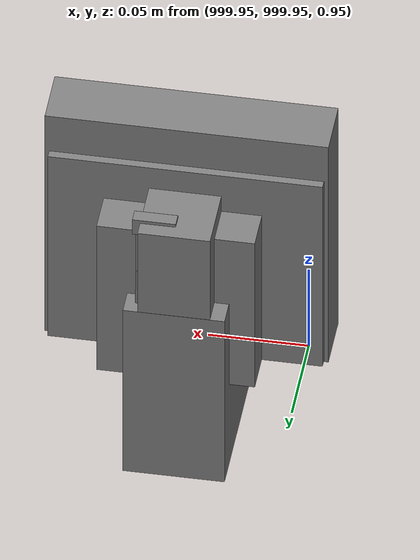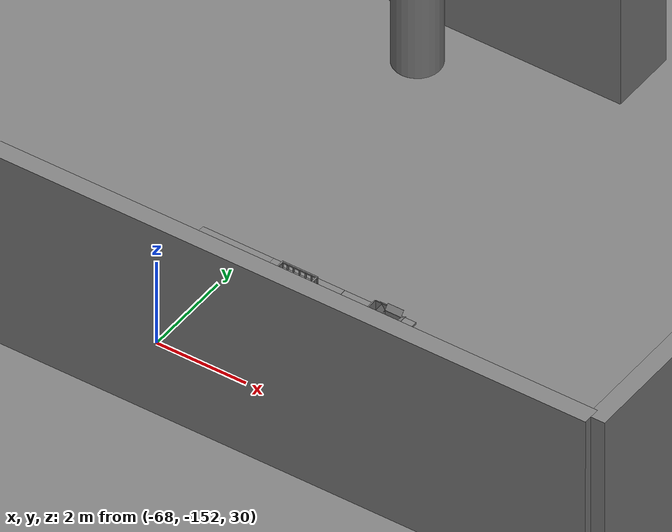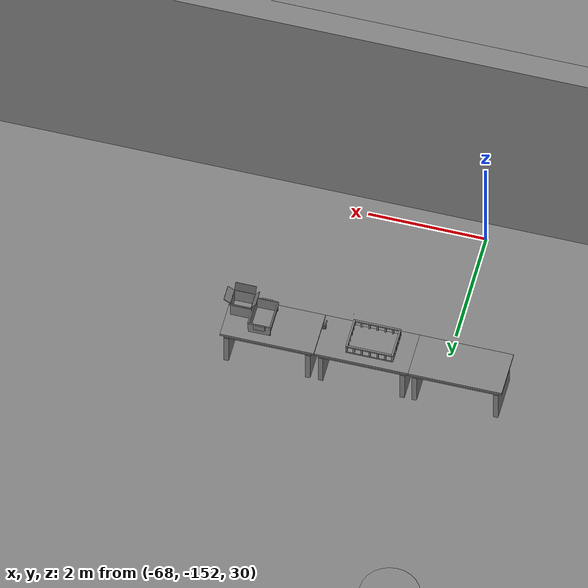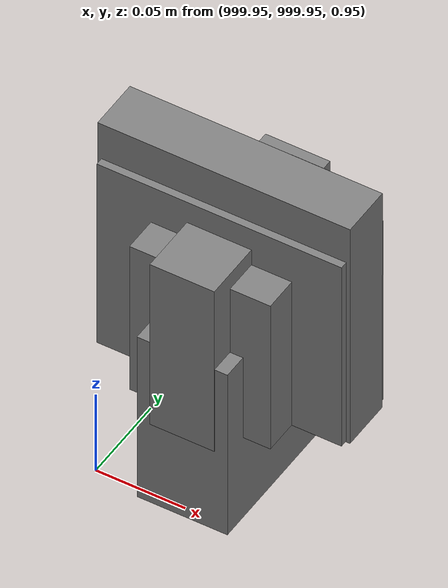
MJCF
<mujoco>
    <option gravity="0.000000000 0.000000000 -9.810000420" timestep="0.0049999999" integrator="implicitfast" density="1.225" viscosity="1.8000001e-05" noslip_iterations="10" iterations="100" sdf_iterations="50">
        <flag multiccd="disable"/>
    </option>
    <size memory="1000M"/>
    <compiler coordinate="local"/>
    <worldbody>
        <light cutoff="30" pos="0 1 1" dir="0 -1 -2"/>
        <light cutoff="30" pos="0 -1 1" dir="0 1 -2"/>
        <body pos="-64.866622925 -149.383972168 30.183746338" euler="89.999984741 89.999946594 0.000000000" name="openloong_gripper_2f85_fix_base_usda_bluebox_01">
            <geom contype="1" conaffinity="1" density="1000" type="box" material="" rgba="0.500000000 0.500000000 0.500000000 1.000000000" solimp="0.899999976 0.949999988 0.001000000" friction="1.000000000 0.005000000 0.000100000" solref="0.020000000 1.000000000" margin="0" condim="3" group="0" pos="0.276580811 0.187225342 0.000068665" quat="0.707106948 0.000077471 0.707106352 0.000077486" size="0.100000001 0.057999998 0.010000000" name="openloong_gripper_2f85_fix_base_usda_geom_7B746A93_C2F4_4278_9B76_FBB6C5C6402D"/>
            <geom contype="1" conaffinity="1" density="1000" type="box" material="" rgba="0.500000000 0.500000000 0.500000000 1.000000000" solimp="0.899999976 0.949999988 0.001000000" friction="1.000000000 0.005000000 0.000100000" solref="0.020000000 1.000000000" margin="0" condim="3" group="0" pos="0.000000000 0.002883911 0.000000000" quat="0.999999881 0.000000000 0.000000000 0.000000000" size="0.254000008 0.003000000 0.172000006" name="openloong_gripper_2f85_fix_base_usda_geom_2A85A6F9_7A59_401F_8F67_7819A5DAD951"/>
            <geom contype="1" conaffinity="1" density="1000" type="box" material="" rgba="0.500000000 0.500000000 0.500000000 1.000000000" solimp="0.899999976 0.949999988 0.001000000" friction="1.000000000 0.005000000 0.000100000" solref="0.020000000 1.000000000" margin="0" condim="3" group="0" pos="0.000000000 0.124874115 0.173484802" quat="0.999796331 0.020176515 -0.000000015 0.000000030" size="0.259999990 0.119999997 0.007000000" name="openloong_gripper_2f85_fix_base_usda_geom_AF486BE2_8274_43A5_AEE0_6CA9F76C024D"/>
            <geom contype="1" conaffinity="1" density="1000" type="box" material="" rgba="0.500000000 0.500000000 0.500000000 1.000000000" solimp="0.899999976 0.949999988 0.001000000" friction="1.000000000 0.005000000 0.000100000" solref="0.020000000 1.000000000" margin="0" condim="3" group="0" pos="0.000000000 0.124874115 -0.173469543" quat="0.999796331 -0.020176545 -0.000000015 0.000000000" size="0.259999990 0.119999997 0.007000000" name="openloong_gripper_2f85_fix_base_usda_geom_1BE68973_3479_4C2B_B1D4_5C0B7E3BBC4E"/>
            <geom contype="1" conaffinity="1" density="1000" type="box" material="" rgba="0.500000000 0.500000000 0.500000000 1.000000000" solimp="0.899999976 0.949999988 0.001000000" friction="1.000000000 0.005000000 0.000100000" solref="0.020000000 1.000000000" margin="0" condim="3" group="0" pos="0.000000000 0.214008331 0.188980103" quat="0.999912977 0.013176724 0.000000015 0.000000000" size="0.259999990 0.029999999 0.012500000" name="openloong_gripper_2f85_fix_base_usda_geom_22840341_F953_44B0_A16A_664CF28DFFB5"/>
            <geom contype="1" conaffinity="1" density="1000" type="box" material="" rgba="0.500000000 0.500000000 0.500000000 1.000000000" solimp="0.899999976 0.949999988 0.001000000" friction="1.000000000 0.005000000 0.000100000" solref="0.020000000 1.000000000" margin="0" condim="3" group="0" pos="-0.258361816 0.125289917 0.001876831" quat="0.702796936 -0.020792112 0.710783124 0.020769298" size="0.189999998 0.119999997 0.009000000" name="openloong_gripper_2f85_fix_base_usda_geom_12C25F4A_FDA8_4A54_98EA_11012E45AD92"/>
            <geom contype="1" conaffinity="1" density="1000" type="box" material="" rgba="0.500000000 0.500000000 0.500000000 1.000000000" solimp="0.899999976 0.949999988 0.001000000" friction="1.000000000 0.005000000 0.000100000" solref="0.020000000 1.000000000" margin="0" condim="3" group="0" pos="0.000000000 0.214008331 -0.188980103" quat="0.999912977 -0.013176769 0.000000030 0.000000015" size="0.259999990 0.029999999 0.012500000" name="openloong_gripper_2f85_fix_base_usda_geom_73D5FFF9_E2F5_4B1A_8CAA_94DA2C62656D"/>
            <geom contype="1" conaffinity="1" density="1000" type="box" material="" rgba="0.500000000 0.500000000 0.500000000 1.000000000" solimp="0.899999976 0.949999988 0.001000000" friction="1.000000000 0.005000000 0.000100000" solref="0.020000000 1.000000000" margin="0" condim="3" group="0" pos="-0.276611328 0.187225342 0.000068665" quat="0.707106650 0.000077441 0.707106709 0.000077456" size="0.100000001 0.057999998 0.010000000" name="openloong_gripper_2f85_fix_base_usda_geom_9D23E5FE_6692_4F22_9113_D3CFC96C35FF"/>
            <geom contype="1" conaffinity="1" density="1000" type="box" material="" rgba="0.500000000 0.500000000 0.500000000 1.000000000" solimp="0.899999976 0.949999988 0.001000000" friction="1.000000000 0.005000000 0.000100000" solref="0.020000000 1.000000000" margin="0" condim="3" group="0" pos="0.258331299 0.125289917 0.001876831" quat="0.702851415 0.018856421 0.710823774 -0.019329369" size="0.189999998 0.119999997 0.009000000" name="openloong_gripper_2f85_fix_base_usda_geom_AC1E65B8_BEDD_4AB8_912F_7B09D1A09891"/>
            <freejoint name="openloong_gripper_2f85_fix_base_usda_bluebox_01_joint"/>
            <site size="0.005000000 0.005000000 0.005000000" rgba="0.500000000 0.500000000 0.500000000 1.000000000" pos="0.000000000 0.000000000 0.000000000" quat="0.999961913 0.008726534 0.000000000 0.000000000" group="0" type="sphere" name="openloong_gripper_2f85_fix_base_usda_bluebox_01site"/>
        </body>
        <body pos="-64.496299744 -149.491867065 30.235729218" euler="0.000000000 0.000000000 89.999946594" name="openloong_gripper_2f85_fix_base_usda_cardboardbox_01">
            <geom contype="1" conaffinity="1" density="1000" type="box" material="" rgba="0.500000000 0.500000000 0.500000000 1.000000000" solimp="0.899999976 0.949999988 0.001000000" friction="1.000000000 0.005000000 0.000100000" solref="0.020000000 1.000000000" margin="0" condim="3" group="0" pos="-0.003166199 -0.004086494 0.005052090" quat="1.000000000 0.000000000 0.000000000 0.000000000" size="0.142499998 0.177500010 0.005000000" name="openloong_gripper_2f85_fix_base_usda_geom_7E57AABD_A44A_446C_B224_AA5301026A1B"/>
            <geom contype="1" conaffinity="1" density="1000" type="box" material="" rgba="0.500000000 0.500000000 0.500000000 1.000000000" solimp="0.899999976 0.949999988 0.001000000" friction="1.000000000 0.005000000 0.000100000" solref="0.020000000 1.000000000" margin="0" condim="3" group="0" pos="-0.003166199 0.170316696 0.150570869" quat="1.000000000 0.000000000 0.000000000 0.000000000" size="0.142499998 0.005000000 0.149999991" name="openloong_gripper_2f85_fix_base_usda_geom_A42AD146_3EC1_4ED8_BC9A_573746D8AD92"/>
            <geom contype="1" conaffinity="1" density="1000" type="box" material="" rgba="0.500000000 0.500000000 0.500000000 1.000000000" solimp="0.899999976 0.949999988 0.001000000" friction="1.000000000 0.005000000 0.000100000" solref="0.020000000 1.000000000" margin="0" condim="3" group="0" pos="-0.147399902 -0.005307198 0.150570869" quat="1.000000000 0.000000000 0.000000000 0.000000000" size="0.005000000 0.177500010 0.149999991" name="openloong_gripper_2f85_fix_base_usda_geom_10B09DFB_5098_44FA_A27C_AC686B2BD8C7"/>
            <geom contype="1" conaffinity="1" density="1000" type="box" material="" rgba="0.500000000 0.500000000 0.500000000 1.000000000" solimp="0.899999976 0.949999988 0.001000000" friction="1.000000000 0.005000000 0.000100000" solref="0.020000000 1.000000000" margin="0" condim="3" group="0" pos="0.140275955 -0.005307198 0.150570869" quat="1.000000000 0.000000000 0.000000000 0.000000000" size="0.005000000 0.177500010 0.149999991" name="openloong_gripper_2f85_fix_base_usda_geom_F26FEC95_4526_44CC_8A8C_B99B58155868"/>
            <geom contype="1" conaffinity="1" density="1000" type="box" material="" rgba="0.500000000 0.500000000 0.500000000 1.000000000" solimp="0.899999976 0.949999988 0.001000000" friction="1.000000000 0.005000000 0.000100000" solref="0.020000000 1.000000000" margin="0" condim="3" group="0" pos="-0.003166199 -0.181550980 0.150570869" quat="1.000000000 0.000000000 0.000000000 0.000000000" size="0.142499998 0.005000000 0.149999991" name="openloong_gripper_2f85_fix_base_usda_geom_C652DBF7_93CE_46E8_8FDD_3801055CC00A"/>
            <freejoint name="openloong_gripper_2f85_fix_base_usda_cardboardbox_01_joint"/>
            <site size="0.005000000 0.005000000 0.005000000" rgba="0.500000000 0.500000000 0.500000000 1.000000000" pos="0.000000000 0.000000000 0.000000000" quat="0.999961913 0.008726535 0.000000000 0.000000000" group="0" type="sphere" name="openloong_gripper_2f85_fix_base_usda_site_99835690_7967_464C_B134_E531B1437A3E"/>
            <body pos="0.139160156 -0.004048347 0.301930904" euler="-179.999954224 49.383502960 179.999954224" name="openloong_gripper_2f85_fix_base_usda_A1_006">
                <geom contype="1" conaffinity="1" density="1000" type="box" material="" rgba="0.500000000 0.500000000 0.500000000 1.000000000" solimp="0.899999976 0.949999988 0.001000000" friction="1.000000000 0.005000000 0.000100000" solref="0.020000000 1.000000000" margin="0" condim="3" group="0" pos="-0.071587563 0.000009537 0.001745224" quat="0.999999881 0.000000000 0.000000000 0.000000000" size="0.071249999 0.179999992 0.002500000" name="openloong_gripper_2f85_fix_base_usda_geom_41E3AD38_9158_41A1_AAFE_AB7DC838EEFE"/>
                <joint armature="0" stiffness="0.07" damping="0.0099999998" axis="0.000000 1.000000 0.000000" type="hinge" name="openloong_gripper_2f85_fix_base_usda_A1_006"/>
            </body>
            <body pos="-0.145902634 -0.004086494 0.301938057" euler="-180.000000000 -60.000011444 -180.000000000" name="openloong_gripper_2f85_fix_base_usda_A2_006">
                <geom contype="1" conaffinity="1" density="1000" type="box" material="" rgba="0.500000000 0.500000000 0.500000000 1.000000000" solimp="0.899999976 0.949999988 0.001000000" friction="1.000000000 0.005000000 0.000100000" solref="0.020000000 1.000000000" margin="0" condim="3" group="0" pos="0.071268082 0.000009537 0.002717972" quat="0.000002921 0.000000000 -0.000000030 0.999999881" size="0.071249999 0.179999992 0.002500000" name="openloong_gripper_2f85_fix_base_usda_geom_2CBB5A1D_AB3B_45BE_A437_A8F721965362"/>
                <joint armature="0" stiffness="0.07" damping="0.0099999998" axis="0.000000 1.000000 0.000000" type="hinge" name="openloong_gripper_2f85_fix_base_usda_A2_006"/>
            </body>
            <body pos="-0.003385544 0.175991058 0.301930904" euler="-125.858116150 -0.000004561 0.000002331" name="openloong_gripper_2f85_fix_base_usda_B2_006">
                <geom contype="1" conaffinity="1" density="1000" type="box" material="" rgba="0.500000000 0.500000000 0.500000000 1.000000000" solimp="0.899999976 0.949999988 0.001000000" friction="1.000000000 0.005000000 0.000100000" solref="0.020000000 1.000000000" margin="0" condim="3" group="0" pos="0.000009537 -0.070939064 -0.002470016" quat="0.999614120 0.027776197 -0.000000015 0.000000030" size="0.137500003 0.064999998 0.005000000" name="openloong_gripper_2f85_fix_base_usda_geom_AE8BE435_04A8_46BC_9C9D_81EA00C693B6"/>
                <joint armature="0" stiffness="0.07" damping="0.0099999998" axis="1.000000 0.000000 0.000000" type="hinge" name="openloong_gripper_2f85_fix_base_usda_B2_006"/>
            </body>
            <body pos="-0.003385544 -0.184140205 0.301938057" euler="147.805557251 0.000000000 0.000000000" name="openloong_gripper_2f85_fix_base_usda_B1_006">
                <geom contype="1" conaffinity="1" density="1000" type="box" material="" rgba="0.500000000 0.500000000 0.500000000 1.000000000" solimp="0.899999976 0.949999988 0.001000000" friction="1.000000000 0.005000000 0.000100000" solref="0.020000000 1.000000000" margin="0" condim="3" group="0" pos="-0.000028610 0.070202351 -0.002703667" quat="0.999614179 -0.027776167 0.000000000 0.000000000" size="0.137500003 0.064999998 0.005000000" name="openloong_gripper_2f85_fix_base_usda_geom_6406CC4B_9124_4038_814B_579C968D688C"/>
                <joint armature="0" stiffness="0.07" damping="0.0099999998" axis="1.000000 0.000000 0.000000" type="hinge" name="openloong_gripper_2f85_fix_base_usda_B1_006"/>
            </body>
        </body>
        <body pos="-65.882858276 -149.481979370 30.229999542" euler="-64.487716675 0.000000000 0.000000000" name="openloong_gripper_2f85_fix_base_usda_Barcode">
            <geom contype="1" conaffinity="1" density="1000" type="box" material="" rgba="0.500000000 0.500000000 0.500000000 1.000000000" solimp="0.899999976 0.949999988 0.001000000" friction="1.000000000 0.005000000 0.000100000" solref="0.020000000 1.000000000" margin="0" condim="3" group="0" pos="0.000000000 0.013038635 0.001419067" quat="0.000000000 0.000000000 0.000000000 1.000000119" size="0.034000002 0.010000000 0.017999999" name="openloong_gripper_2f85_fix_base_usda_geom_2583E4AF_4497_46E3_BC64_2CB669B02498"/>
            <geom contype="1" conaffinity="1" density="1000" type="box" material="" rgba="0.500000000 0.500000000 0.500000000 1.000000000" solimp="0.899999976 0.949999988 0.001000000" friction="1.000000000 0.005000000 0.000100000" solref="0.020000000 1.000000000" margin="0" condim="3" group="0" pos="0.000000000 -0.035301208 -0.007095337" quat="0.000000000 0.000000000 -0.043619365 0.999048233" size="0.028999999 0.010000000 0.020000000" name="openloong_gripper_2f85_fix_base_usda_geom_FEB737F4_7EFF_49A4_9076_6EBCE8FD5928"/>
            <geom contype="1" conaffinity="1" density="1000" type="box" material="" rgba="0.500000000 0.500000000 0.500000000 1.000000000" solimp="0.899999976 0.949999988 0.001000000" friction="1.000000000 0.005000000 0.000100000" solref="0.020000000 1.000000000" margin="0" condim="3" group="0" pos="0.000000000 -0.043411255 -0.011749268" quat="0.922262907 0.386563420 0.000000000 0.000000000" size="0.026000001 0.010000000 0.020000000" name="openloong_gripper_2f85_fix_base_usda_geom_2ECF6201_B090_4859_A904_9BBF7AF83FF1"/>
            <geom contype="1" conaffinity="1" density="1000" type="box" material="" rgba="0.500000000 0.500000000 0.500000000 1.000000000" solimp="0.899999976 0.949999988 0.001000000" friction="1.000000000 0.005000000 0.000100000" solref="0.020000000 1.000000000" margin="0" condim="3" group="0" pos="0.000000000 -0.016967773 -0.031860352" quat="0.000000000 0.000000000 0.000000000 1.000000119" size="0.008000000 0.010000000 0.013000000" name="openloong_gripper_2f85_fix_base_usda_geom_21C5A7FD_3AA5_41DA_912C_EDC70BF30EE0"/>
            <geom contype="1" conaffinity="1" density="1000" type="box" material="" rgba="0.500000000 0.500000000 0.500000000 1.000000000" solimp="0.899999976 0.949999988 0.001000000" friction="1.000000000 0.005000000 0.000100000" solref="0.020000000 1.000000000" margin="0" condim="3" group="0" pos="0.000000000 -0.001869202 0.000312805" quat="0.953716993 0.300705761 0.000000000 0.000000000" size="0.032000002 0.010000000 0.018999999" name="openloong_gripper_2f85_fix_base_usda_geom_7531C366_29C8_4096_B2EE_F32A2EDDBA28"/>
            <geom contype="1" conaffinity="1" density="1000" type="box" material="" rgba="0.500000000 0.500000000 0.500000000 1.000000000" solimp="0.899999976 0.949999988 0.001000000" friction="1.000000000 0.005000000 0.000100000" solref="0.020000000 1.000000000" margin="0" condim="3" group="0" pos="0.000000000 -0.019531250 -0.003173828" quat="0.953716993 0.300705761 0.000000000 0.000000000" size="0.030999999 0.010000000 0.020000000" name="openloong_gripper_2f85_fix_base_usda_geom_F3A2CAD1_1909_4182_B978_6D9175EEF9CA"/>
            <geom contype="1" conaffinity="1" density="1000" type="box" material="" rgba="0.500000000 0.500000000 0.500000000 1.000000000" solimp="0.899999976 0.949999988 0.001000000" friction="1.000000000 0.005000000 0.000100000" solref="0.020000000 1.000000000" margin="0" condim="3" group="0" pos="0.000000000 -0.035301208 -0.007095337" quat="0.953716993 0.300705761 0.000000000 0.000000000" size="0.028999999 0.010000000 0.020000000" name="openloong_gripper_2f85_fix_base_usda_geom_FB248F15_9968_40D4_AF0B_3107AE3F70F7"/>
            <geom contype="1" conaffinity="1" density="1000" type="box" material="" rgba="0.500000000 0.500000000 0.500000000 1.000000000" solimp="0.899999976 0.949999988 0.001000000" friction="1.000000000 0.005000000 0.000100000" solref="0.020000000 1.000000000" margin="0" condim="3" group="0" pos="0.000000000 -0.042617798 -0.071121216" quat="0.000000000 0.000000000 0.000000000 1.000000119" size="0.013000000 0.021000000 0.059999999" name="openloong_gripper_2f85_fix_base_usda_geom_2B1240F5_213B_4DCD_8D51_6083207FBAE4"/>
            <freejoint name="openloong_gripper_2f85_fix_base_usda_Barcode_joint"/>
            <site size="0.005000000 0.005000000 0.005000000" rgba="0.500000000 0.500000000 0.500000000 1.000000000" pos="0.000000000 0.000000000 0.000000000" quat="1.000000000 0.000000000 0.000000000 0.000000000" group="0" type="sphere" name="openloong_gripper_2f85_fix_base_usda_Barcode_site"/>
        </body>
        <body pos="-66.745018005 -149.392349243 30.184000015" euler="0.000000000 0.000000000 89.999946594" name="[22333790621734]_Basket_01">
            <geom contype="1" conaffinity="1" density="1000" type="box" material="" rgba="0.500000000 0.500000000 0.500000000 1.000000000" solimp="0.899999976 0.949999988 0.001000000" friction="1.000000000 0.005000000 0.000100000" solref="0.020000000 1.000000000" margin="0" condim="3" group="0" pos="-0.052425385 0.389207840 0.089787483" quat="0.707107008 0.000000000 0.000000000 0.707106411" size="0.014249999 0.014249999 0.059999999" name="[22333790621734]_geom_11A3C263_ECAB_4903_9B33_AA83DED49F4E"/>
            <geom contype="1" conaffinity="1" density="1000" type="box" material="" rgba="0.500000000 0.500000000 0.500000000 1.000000000" solimp="0.899999976 0.949999988 0.001000000" friction="1.000000000 0.005000000 0.000100000" solref="0.020000000 1.000000000" margin="0" condim="3" group="0" pos="0.264015198 -0.133043289 0.089787483" quat="0.707107008 0.000000000 0.000000000 0.707106411" size="0.014249999 0.014249999 0.059999999" name="[22333790621734]_geom_D2247EC9_1030_4262_B538_24061D8E1FA4"/>
            <geom contype="1" conaffinity="1" density="1000" type="box" material="" rgba="0.500000000 0.500000000 0.500000000 1.000000000" solimp="0.899999976 0.949999988 0.001000000" friction="1.000000000 0.005000000 0.000100000" solref="0.020000000 1.000000000" margin="0" condim="3" group="0" pos="-0.264015198 -0.265548706 0.089793205" quat="0.707107008 0.000000000 0.000000000 0.707106411" size="0.014249999 0.014249999 0.059999999" name="[22333790621734]_geom_C65D25FA_6640_4CFC_A664_8AA3A58394E9"/>
            <geom contype="1" conaffinity="1" density="1000" type="box" material="" rgba="0.500000000 0.500000000 0.500000000 1.000000000" solimp="0.899999976 0.949999988 0.001000000" friction="1.000000000 0.005000000 0.000100000" solref="0.020000000 1.000000000" margin="0" condim="3" group="0" pos="-0.160263062 -0.389322281 0.089793205" quat="0.707107008 0.000000000 0.000000000 0.707106411" size="0.014249999 0.014249999 0.059999999" name="[22333790621734]_geom_BA247F7D_EF9A_4293_B50B_0C3C5FC6BCFB"/>
            <geom contype="1" conaffinity="1" density="1000" type="box" material="" rgba="0.500000000 0.500000000 0.500000000 1.000000000" solimp="0.899999976 0.949999988 0.001000000" friction="1.000000000 0.005000000 0.000100000" solref="0.020000000 1.000000000" margin="0" condim="3" group="0" pos="0.162265778 -0.389322281 0.089787483" quat="0.707107008 0.000000000 0.000000000 0.707106411" size="0.014249999 0.014249999 0.059999999" name="[22333790621734]_geom_37166857_66CF_44FB_9EBD_79B12542CC1B"/>
            <geom contype="1" conaffinity="1" density="1000" type="box" material="" rgba="0.500000000 0.500000000 0.500000000 1.000000000" solimp="0.899999976 0.949999988 0.001000000" friction="1.000000000 0.005000000 0.000100000" solref="0.020000000 1.000000000" margin="0" condim="3" group="0" pos="0.264015198 0.389207840 0.089787483" quat="0.707107008 0.000000000 0.000000000 0.707106411" size="0.014249999 0.014249999 0.059999999" name="[22333790621734]_geom_D2691FF0_22E4_4C07_A300_5285B760537E"/>
            <geom contype="1" conaffinity="1" density="1000" type="box" material="" rgba="0.500000000 0.500000000 0.500000000 1.000000000" solimp="0.899999976 0.949999988 0.001000000" friction="1.000000000 0.005000000 0.000100000" solref="0.020000000 1.000000000" margin="0" condim="3" group="0" pos="-0.264015198 -0.133043289 0.089793205" quat="0.707107008 0.000000000 0.000000000 0.707106411" size="0.014249999 0.014249999 0.059999999" name="[22333790621734]_geom_0DFAB3A8_0C95_4345_9C3E_DB8ABA4BB9BB"/>
            <geom contype="1" conaffinity="1" density="1000" type="box" material="" rgba="0.500000000 0.500000000 0.500000000 1.000000000" solimp="0.899999976 0.949999988 0.001000000" friction="1.000000000 0.005000000 0.000100000" solref="0.020000000 1.000000000" margin="0" condim="3" group="0" pos="-0.264026642 0.269256592 0.089793205" quat="0.707107008 0.000000000 0.000000000 0.707106411" size="0.014249999 0.014249999 0.059999999" name="[22333790621734]_geom_93503780_BBAD_4684_9AD8_8819CDBDB3C1"/>
            <geom contype="1" conaffinity="1" density="1000" type="box" material="" rgba="0.500000000 0.500000000 0.500000000 1.000000000" solimp="0.899999976 0.949999988 0.001000000" friction="1.000000000 0.005000000 0.000100000" solref="0.020000000 1.000000000" margin="0" condim="3" group="0" pos="0.054462433 0.389207840 0.089787483" quat="0.707107008 0.000000000 0.000000000 0.707106411" size="0.014249999 0.014249999 0.059999999" name="[22333790621734]_geom_C294BB39_E3DB_4FFB_939A_A2FE4A187BE0"/>
            <geom contype="1" conaffinity="1" density="1000" type="box" material="" rgba="0.500000000 0.500000000 0.500000000 1.000000000" solimp="0.899999976 0.949999988 0.001000000" friction="1.000000000 0.005000000 0.000100000" solref="0.020000000 1.000000000" margin="0" condim="3" group="0" pos="0.054462433 -0.389322281 0.089787483" quat="0.707107008 0.000000000 0.000000000 0.707106411" size="0.014249999 0.014249999 0.059999999" name="[22333790621734]_geom_8F957A7C_2784_4630_9E84_22BBF0850A64"/>
            <geom contype="1" conaffinity="1" density="1000" type="box" material="" rgba="0.500000000 0.500000000 0.500000000 1.000000000" solimp="0.899999976 0.949999988 0.001000000" friction="1.000000000 0.005000000 0.000100000" solref="0.020000000 1.000000000" margin="0" condim="3" group="0" pos="0.264015198 0.269256592 0.089793205" quat="0.707107008 0.000000000 0.000000000 0.707106411" size="0.014249999 0.014249999 0.059999999" name="[22333790621734]_geom_0EBCF3D4_5B88_48EB_8228_37C82DB4AB16"/>
            <geom contype="1" conaffinity="1" density="1000" type="box" material="" rgba="0.500000000 0.500000000 0.500000000 1.000000000" solimp="0.899999976 0.949999988 0.001000000" friction="1.000000000 0.005000000 0.000100000" solref="0.020000000 1.000000000" margin="0" condim="3" group="0" pos="0.264015198 -0.389322281 0.089787483" quat="0.707107008 0.000000000 0.000000000 0.707106411" size="0.014249999 0.014249999 0.059999999" name="[22333790621734]_geom_E7439405_9FA3_417C_90C7_0D86DAD1D628"/>
            <geom contype="1" conaffinity="1" density="1000" type="box" material="" rgba="0.500000000 0.500000000 0.500000000 1.000000000" solimp="0.899999976 0.949999988 0.001000000" friction="1.000000000 0.005000000 0.000100000" solref="0.020000000 1.000000000" margin="0" condim="3" group="0" pos="0.000000000 0.000000000 0.015998840" quat="0.707107008 0.000000000 0.000000000 0.707106411" size="0.403499991 0.279000014 0.015750000" name="[22333790621734]_geom_1EF22872_548B_468F_B2A5_44A39F1F442E"/>
            <geom contype="1" conaffinity="1" density="1000" type="box" material="" rgba="0.500000000 0.500000000 0.500000000 1.000000000" solimp="0.899999976 0.949999988 0.001000000" friction="1.000000000 0.005000000 0.000100000" solref="0.020000000 1.000000000" margin="0" condim="3" group="0" pos="0.000000000 -0.389476776 0.163619041" quat="0.707107008 0.000000000 0.000000000 0.707106411" size="0.015000000 0.277500004 0.015750000" name="[22333790621734]_geom_942E0211_B4F0_4C1A_9D10_E4F98EA7130A"/>
            <geom contype="1" conaffinity="1" density="1000" type="box" material="" rgba="0.500000000 0.500000000 0.500000000 1.000000000" solimp="0.899999976 0.949999988 0.001000000" friction="1.000000000 0.005000000 0.000100000" solref="0.020000000 1.000000000" margin="0" condim="3" group="0" pos="0.162265778 0.389207840 0.089787483" quat="0.707107008 0.000000000 0.000000000 0.707106411" size="0.014249999 0.014249999 0.059999999" name="[22333790621734]_geom_F65E4E3E_5FB3_48F6_87E1_4566AA2F1633"/>
            <geom contype="1" conaffinity="1" density="1000" type="box" material="" rgba="0.500000000 0.500000000 0.500000000 1.000000000" solimp="0.899999976 0.949999988 0.001000000" friction="1.000000000 0.005000000 0.000100000" solref="0.020000000 1.000000000" margin="0" condim="3" group="0" pos="0.000000000 0.389471054 0.163619041" quat="0.707107008 0.000000000 0.000000000 0.707106411" size="0.015000000 0.277500004 0.015750000" name="[22333790621734]_geom_682FC137_1602_4DF7_8B69_F74F0B0A0384"/>
            <geom contype="1" conaffinity="1" density="1000" type="box" material="" rgba="0.500000000 0.500000000 0.500000000 1.000000000" solimp="0.899999976 0.949999988 0.001000000" friction="1.000000000 0.005000000 0.000100000" solref="0.020000000 1.000000000" margin="0" condim="3" group="0" pos="-0.263511658 0.000000000 0.163619041" quat="0.707107008 0.000000000 0.000000000 0.707106411" size="0.403499991 0.015000000 0.015750000" name="[22333790621734]_geom_18C381F3_A16F_4EA8_A4DD_C81AC65D9075"/>
            <geom contype="1" conaffinity="1" density="1000" type="box" material="" rgba="0.500000000 0.500000000 0.500000000 1.000000000" solimp="0.899999976 0.949999988 0.001000000" friction="1.000000000 0.005000000 0.000100000" solref="0.020000000 1.000000000" margin="0" condim="3" group="0" pos="-0.264015198 0.141334534 0.089793205" quat="0.707107008 0.000000000 0.000000000 0.707106411" size="0.014249999 0.014249999 0.059999999" name="[22333790621734]_geom_3478CBCC_B4B7_452F_A596_3B26B9A770FC"/>
            <geom contype="1" conaffinity="1" density="1000" type="box" material="" rgba="0.500000000 0.500000000 0.500000000 1.000000000" solimp="0.899999976 0.949999988 0.001000000" friction="1.000000000 0.005000000 0.000100000" solref="0.020000000 1.000000000" margin="0" condim="3" group="0" pos="0.264015198 -0.265548706 0.089787483" quat="0.707107008 0.000000000 0.000000000 0.707106411" size="0.014249999 0.014249999 0.059999999" name="[22333790621734]_geom_E7A60815_571C_46D6_857D_F634CFC030AF"/>
            <geom contype="1" conaffinity="1" density="1000" type="box" material="" rgba="0.500000000 0.500000000 0.500000000 1.000000000" solimp="0.899999976 0.949999988 0.001000000" friction="1.000000000 0.005000000 0.000100000" solref="0.020000000 1.000000000" margin="0" condim="3" group="0" pos="-0.160263062 0.389207840 0.089787483" quat="0.707107008 0.000000000 0.000000000 0.707106411" size="0.014249999 0.014249999 0.059999999" name="[22333790621734]_geom_E7163FA8_28DB_4629_AED6_A4A0AF0BACAE"/>
            <geom contype="1" conaffinity="1" density="1000" type="box" material="" rgba="0.500000000 0.500000000 0.500000000 1.000000000" solimp="0.899999976 0.949999988 0.001000000" friction="1.000000000 0.005000000 0.000100000" solref="0.020000000 1.000000000" margin="0" condim="3" group="0" pos="-0.052425385 -0.389322281 0.089787483" quat="0.707107008 0.000000000 0.000000000 0.707106411" size="0.014249999 0.014249999 0.059999999" name="[22333790621734]_geom_FAFAE344_336E_441E_BDFE_86CC83C60A2D"/>
            <geom contype="1" conaffinity="1" density="1000" type="box" material="" rgba="0.500000000 0.500000000 0.500000000 1.000000000" solimp="0.899999976 0.949999988 0.001000000" friction="1.000000000 0.005000000 0.000100000" solref="0.020000000 1.000000000" margin="0" condim="3" group="0" pos="-0.264026642 -0.389322281 0.089793205" quat="0.707107008 0.000000000 0.000000000 0.707106411" size="0.014249999 0.014249999 0.059999999" name="[22333790621734]_geom_F9281CCD_0AA3_447B_8F1D_38F66C76EA94"/>
            <geom contype="1" conaffinity="1" density="1000" type="box" material="" rgba="0.500000000 0.500000000 0.500000000 1.000000000" solimp="0.899999976 0.949999988 0.001000000" friction="1.000000000 0.005000000 0.000100000" solref="0.020000000 1.000000000" margin="0" condim="3" group="0" pos="0.264015198 0.141334534 0.089787483" quat="0.707107008 0.000000000 0.000000000 0.707106411" size="0.014249999 0.014249999 0.059999999" name="[22333790621734]_geom_92BBC4A5_59BF_4FD9_86B2_8F14FA3BA438"/>
            <geom contype="1" conaffinity="1" density="1000" type="box" material="" rgba="0.500000000 0.500000000 0.500000000 1.000000000" solimp="0.899999976 0.949999988 0.001000000" friction="1.000000000 0.005000000 0.000100000" solref="0.020000000 1.000000000" margin="0" condim="3" group="0" pos="-0.264015198 0.389207840 0.089793205" quat="0.707107008 0.000000000 0.000000000 0.707106411" size="0.014249999 0.014249999 0.059999999" name="[22333790621734]_geom_A2E00794_FEB1_4308_80D8_A70F4F10093A"/>
            <geom contype="1" conaffinity="1" density="1000" type="box" material="" rgba="0.500000000 0.500000000 0.500000000 1.000000000" solimp="0.899999976 0.949999988 0.001000000" friction="1.000000000 0.005000000 0.000100000" solref="0.020000000 1.000000000" margin="0" condim="3" group="0" pos="0.264015198 0.004480362 0.089787483" quat="0.707107008 0.000000000 0.000000000 0.707106411" size="0.014249999 0.014249999 0.059999999" name="[22333790621734]_geom_1E8624FB_F324_43F4_9D79_A5CC29816744"/>
            <geom contype="1" conaffinity="1" density="1000" type="box" material="" rgba="0.500000000 0.500000000 0.500000000 1.000000000" solimp="0.899999976 0.949999988 0.001000000" friction="1.000000000 0.005000000 0.000100000" solref="0.020000000 1.000000000" margin="0" condim="3" group="0" pos="0.263694763 -0.000011444 0.163619041" quat="0.707107008 0.000000000 0.000000000 0.707106411" size="0.403499991 0.015000000 0.015750000" name="[22333790621734]_geom_00B15D3E_547D_4C3E_A1BD_286FB0C2F10F"/>
            <geom contype="1" conaffinity="1" density="1000" type="box" material="" rgba="0.500000000 0.500000000 0.500000000 1.000000000" solimp="0.899999976 0.949999988 0.001000000" friction="1.000000000 0.005000000 0.000100000" solref="0.020000000 1.000000000" margin="0" condim="3" group="0" pos="-0.264015198 0.004480362 0.089793205" quat="0.707107008 0.000000000 0.000000000 0.707106411" size="0.014249999 0.014249999 0.059999999" name="[22333790621734]_geom_570878E2_3847_4E1F_BC09_DD36E2AF57FC"/>
            <freejoint name="[22333790621734]_joint_65C33C53_4466_4941_9919_07EABBDB579F"/>
        </body>
        <body pos="0.000000000 0.000000000 0.000000000" euler="0.000000000 0.000000000 0.000000000" name="Static Objects_Static Objects">
            <geom contype="1" conaffinity="1" density="1000" type="box" material="" rgba="0.500000000 0.500000000 0.500000000 1.000000000" solimp="0.899999976 0.949999988 0.001000000" friction="1.000000000 0.005000000 0.000100000" solref="0.020000000 1.000000000" margin="0" condim="3" group="0" pos="-67.544113159 -149.365814209 29.727830887" quat="0.500000417 0.499999970 0.499999553 0.499999970" size="0.381000012 0.319999993 0.041000001" name="Static Objects_geom_F1FA102F_A7BB_4A5D_9EEA_63AF82A36417"/>
            <geom contype="1" conaffinity="1" density="1000" type="box" material="" rgba="0.500000000 0.500000000 0.500000000 1.000000000" solimp="0.899999976 0.949999988 0.001000000" friction="1.000000000 0.005000000 0.000100000" solref="0.020000000 1.000000000" margin="0" condim="3" group="0" pos="-68.239501953 -149.365814209 30.086868286" quat="0.500000417 0.499999970 0.499999553 0.499999970" size="0.370999992 0.039500002 0.745000005" name="Static Objects_geom_8833683E_B35B_462E_B9D7_24CABB97DA94"/>
            <geom contype="1" conaffinity="1" density="1000" type="box" material="" rgba="0.500000000 0.500000000 0.500000000 1.000000000" solimp="0.899999976 0.949999988 0.001000000" friction="1.000000000 0.005000000 0.000100000" solref="0.020000000 1.000000000" margin="0" condim="3" group="0" pos="-68.239501953 -149.365814209 30.147235870" quat="0.500000417 0.499999970 0.499999553 0.499999970" size="0.400000006 0.022000000 0.800000012" name="Static Objects_geom_B50FF0BB_97DC_45B3_A2D0_CF6669296734"/>
            <geom contype="1" conaffinity="1" density="1000" type="box" material="" rgba="0.500000000 0.500000000 0.500000000 1.000000000" solimp="0.899999976 0.949999988 0.001000000" friction="1.000000000 0.005000000 0.000100000" solref="0.020000000 1.000000000" margin="0" condim="3" group="0" pos="-68.934890747 -149.365814209 29.727830887" quat="0.500000417 0.499999970 0.499999553 0.499999970" size="0.381000012 0.319999993 0.041000001" name="Static Objects_geom_8E47DA03_EE51_4252_98B1_75C7E272F344"/>
            <geom contype="1" conaffinity="1" density="1000" type="box" material="" rgba="0.500000000 0.500000000 0.500000000 1.000000000" solimp="0.899999976 0.949999988 0.001000000" friction="1.000000000 0.005000000 0.000100000" solref="0.020000000 1.000000000" margin="0" condim="3" group="0" pos="-68.239501953 -149.365814209 29.561563492" quat="0.500000417 0.499999970 0.499999553 0.499999970" size="0.020000000 0.022000000 0.660000026" name="Static Objects_geom_0E463A6E_181B_473C_8574_DBC14862756B"/>
            <geom contype="1" conaffinity="1" density="1000" type="box" material="" rgba="0.500000000 0.500000000 0.500000000 1.000000000" solimp="0.899999976 0.949999988 0.001000000" friction="1.000000000 0.005000000 0.000100000" solref="0.020000000 1.000000000" margin="0" condim="3" group="0" pos="-65.945671082 -149.365814209 29.727830887" quat="0.500000417 0.499999970 0.499999553 0.499999970" size="0.381000012 0.319999993 0.041000001" name="Static Objects_geom_3F563A07_63B3_465E_A3FA_8AD51FB1085A"/>
            <geom contype="1" conaffinity="1" density="1000" type="box" material="" rgba="0.500000000 0.500000000 0.500000000 1.000000000" solimp="0.899999976 0.949999988 0.001000000" friction="1.000000000 0.005000000 0.000100000" solref="0.020000000 1.000000000" margin="0" condim="3" group="0" pos="-66.641059875 -149.365814209 30.086868286" quat="0.500000417 0.499999970 0.499999553 0.499999970" size="0.370999992 0.039500002 0.745000005" name="Static Objects_geom_A87075E6_6A11_4D69_A71D_B613131725AF"/>
            <geom contype="1" conaffinity="1" density="1000" type="box" material="" rgba="0.500000000 0.500000000 0.500000000 1.000000000" solimp="0.899999976 0.949999988 0.001000000" friction="1.000000000 0.005000000 0.000100000" solref="0.020000000 1.000000000" margin="0" condim="3" group="0" pos="-66.641059875 -149.365814209 30.147235870" quat="0.500000417 0.499999970 0.499999553 0.499999970" size="0.400000006 0.022000000 0.800000012" name="Static Objects_geom_E2C164D4_7CFB_4D94_920B_D2D4E0FF1603"/>
            <geom contype="1" conaffinity="1" density="1000" type="box" material="" rgba="0.500000000 0.500000000 0.500000000 1.000000000" solimp="0.899999976 0.949999988 0.001000000" friction="1.000000000 0.005000000 0.000100000" solref="0.020000000 1.000000000" margin="0" condim="3" group="0" pos="-67.336448669 -149.365814209 29.727830887" quat="0.500000417 0.499999970 0.499999553 0.499999970" size="0.381000012 0.319999993 0.041000001" name="Static Objects_geom_424AF033_182F_462B_AF2A_1FEA60BDC4C0"/>
            <geom contype="1" conaffinity="1" density="1000" type="box" material="" rgba="0.500000000 0.500000000 0.500000000 1.000000000" solimp="0.899999976 0.949999988 0.001000000" friction="1.000000000 0.005000000 0.000100000" solref="0.020000000 1.000000000" margin="0" condim="3" group="0" pos="-66.641059875 -149.365814209 29.561563492" quat="0.500000417 0.499999970 0.499999553 0.499999970" size="0.020000000 0.022000000 0.660000026" name="Static Objects_geom_08CD80A5_A45B_4409_A321_AD4B0EA2129A"/>
            <geom contype="1" conaffinity="1" density="1000" type="box" material="" rgba="0.500000000 0.500000000 0.500000000 1.000000000" solimp="0.899999976 0.949999988 0.001000000" friction="1.000000000 0.005000000 0.000100000" solref="0.020000000 1.000000000" margin="0" condim="3" group="0" pos="-64.338577271 -149.365814209 29.727830887" quat="0.500000417 0.499999970 0.499999553 0.499999970" size="0.381000012 0.319999993 0.041000001" name="Static Objects_geom_393B4D18_EC0D_4B73_A6D1_68D4EE7425BC"/>
            <geom contype="1" conaffinity="1" density="1000" type="box" material="" rgba="0.500000000 0.500000000 0.500000000 1.000000000" solimp="0.899999976 0.949999988 0.001000000" friction="1.000000000 0.005000000 0.000100000" solref="0.020000000 1.000000000" margin="0" condim="3" group="0" pos="-65.033966064 -149.365814209 30.086868286" quat="0.500000417 0.499999970 0.499999553 0.499999970" size="0.370999992 0.039500002 0.745000005" name="Static Objects_geom_3F382E03_3DDF_45EB_B03C_98FA5484E2EE"/>
            <geom contype="1" conaffinity="1" density="1000" type="box" material="" rgba="0.500000000 0.500000000 0.500000000 1.000000000" solimp="0.899999976 0.949999988 0.001000000" friction="1.000000000 0.005000000 0.000100000" solref="0.020000000 1.000000000" margin="0" condim="3" group="0" pos="-65.033966064 -149.365814209 30.147235870" quat="0.500000417 0.499999970 0.499999553 0.499999970" size="0.400000006 0.022000000 0.800000012" name="Static Objects_geom_F22F4868_339A_48EA_AC71_756E472A92E5"/>
            <geom contype="1" conaffinity="1" density="1000" type="box" material="" rgba="0.500000000 0.500000000 0.500000000 1.000000000" solimp="0.899999976 0.949999988 0.001000000" friction="1.000000000 0.005000000 0.000100000" solref="0.020000000 1.000000000" margin="0" condim="3" group="0" pos="-65.729354858 -149.365814209 29.727830887" quat="0.500000417 0.499999970 0.499999553 0.499999970" size="0.381000012 0.319999993 0.041000001" name="Static Objects_geom_300C6027_B1E5_4532_8841_31BD73F1D3EF"/>
            <geom contype="1" conaffinity="1" density="1000" type="box" material="" rgba="0.500000000 0.500000000 0.500000000 1.000000000" solimp="0.899999976 0.949999988 0.001000000" friction="1.000000000 0.005000000 0.000100000" solref="0.020000000 1.000000000" margin="0" condim="3" group="0" pos="-65.033966064 -149.365814209 29.561563492" quat="0.500000417 0.499999970 0.499999553 0.499999970" size="0.020000000 0.022000000 0.660000026" name="Static Objects_geom_49954DDF_DF08_4F5F_A40F_C99B1B66A74C"/>
            <geom contype="1" conaffinity="1" density="1000" type="box" material="" rgba="0.500000000 0.500000000 0.500000000 1.000000000" solimp="0.899999976 0.949999988 0.001000000" friction="1.000000000 0.005000000 0.000100000" solref="0.020000000 1.000000000" margin="0" condim="3" group="0" pos="-61.754566193 -137.853729248 33.906845093" quat="0.707107067 0.000000000 0.000000000 0.707106471" size="0.759999990 0.759999990 4.500000000" name="Static Objects_geom_E36229E1_10A8_4AA5_865C_D658C4A18F3F"/>
            <geom contype="1" conaffinity="1" density="1000" type="box" material="" rgba="0.500000000 0.500000000 0.500000000 1.000000000" solimp="0.899999976 0.949999988 0.001000000" friction="1.000000000 0.005000000 0.000100000" solref="0.020000000 1.000000000" margin="0" condim="3" group="0" pos="-57.511135101 -144.927108765 31.707921982" quat="1.000000000 0.000000000 0.000000000 0.000000000" size="0.200000003 8.000000000 2.299999952" name="Static Objects_geom_583DC342_2326_4809_A884_59847CDB7567"/>
            <geom contype="1" conaffinity="1" density="1000" type="box" material="" rgba="0.500000000 0.500000000 0.500000000 1.000000000" solimp="0.899999976 0.949999988 0.001000000" friction="1.000000000 0.005000000 0.000100000" solref="0.020000000 1.000000000" margin="0" condim="3" group="0" pos="-80.517646790 -157.574050903 31.688196182" quat="0.707107067 0.000000000 0.000000000 0.707106471" size="0.600000024 0.600000024 2.299999952" name="Static Objects_geom_B7AD5BFF_5A4D_42A8_8BD8_5ED1C9BEB747"/>
            <geom contype="1" conaffinity="1" density="1000" type="box" material="" rgba="0.500000000 0.500000000 0.500000000 1.000000000" solimp="0.899999976 0.949999988 0.001000000" friction="1.000000000 0.005000000 0.000100000" solref="0.020000000 1.000000000" margin="0" condim="3" group="0" pos="-80.711044312 -147.414932251 31.666158676" quat="1.000000000 0.000000000 0.000000000 0.000000000" size="0.200000003 10.000000000 2.299999952" name="Static Objects_geom_54F6B382_AF79_4BC1_9076_1A3ADC0FF324"/>
            <geom contype="1" conaffinity="1" density="1000" type="box" material="" rgba="0.500000000 0.500000000 0.500000000 1.000000000" solimp="0.899999976 0.949999988 0.001000000" friction="1.000000000 0.005000000 0.000100000" solref="0.020000000 1.000000000" margin="0" condim="3" group="0" pos="-57.687217712 -137.434692383 31.688196182" quat="0.707107067 0.000000000 0.000000000 0.707106471" size="0.600000024 0.600000024 2.299999952" name="Static Objects_geom_846D3EC1_82C2_419A_AA92_3AAB11240A76"/>
            <geom contype="1" conaffinity="1" density="1000" type="box" material="" rgba="0.500000000 0.500000000 0.500000000 1.000000000" solimp="0.899999976 0.949999988 0.001000000" friction="1.000000000 0.005000000 0.000100000" solref="0.020000000 1.000000000" margin="0" condim="3" group="0" pos="-69.537033081 -140.263229370 31.714921951" quat="0.707107067 0.000000000 0.000000000 0.707106471" size="0.759999990 4.500000000 2.299999952" name="Static Objects_geom_5C0AD01A_B1F1_43AF_9CF8_2C7C62E4EC19"/>
            <geom contype="1" conaffinity="1" density="1000" type="box" material="" rgba="0.500000000 0.500000000 0.500000000 1.000000000" solimp="0.899999976 0.949999988 0.001000000" friction="1.000000000 0.005000000 0.000100000" solref="0.020000000 1.000000000" margin="0" condim="3" group="0" pos="-80.073638916 -137.853713989 33.906845093" quat="0.707107067 0.000000000 0.000000000 0.707106471" size="0.759999990 0.759999990 4.500000000" name="Static Objects_geom_D7249C6F_EC78_4C0A_8DFB_3025F50A659E"/>
            <geom contype="1" conaffinity="1" density="1000" type="box" material="" rgba="0.500000000 0.500000000 0.500000000 1.000000000" solimp="0.899999976 0.949999988 0.001000000" friction="1.000000000 0.005000000 0.000100000" solref="0.020000000 1.000000000" margin="0" condim="3" group="0" pos="-73.406707764 -155.734664917 31.707921982" quat="1.000000000 0.000000000 0.000000000 0.000000000" size="0.200000003 3.000000000 2.299999952" name="Static Objects_geom_6A2A94A1_60BE_4963_8828_7AE6CE68A6BF"/>
            <geom contype="1" conaffinity="1" density="1000" type="box" material="" rgba="0.500000000 0.500000000 0.500000000 1.000000000" solimp="0.899999976 0.949999988 0.001000000" friction="1.000000000 0.005000000 0.000100000" solref="0.020000000 1.000000000" margin="0" condim="3" group="0" pos="-68.497543335 -137.448257446 31.707921982" quat="0.707107067 0.000000000 0.000000000 0.707106471" size="0.200000003 14.000000000 2.299999952" name="Static Objects_geom_6259A136_2398_4403_9BB9_B9A7EA6D196C"/>
            <geom contype="1" conaffinity="1" density="1000" type="cylinder" material="" rgba="0.500000000 0.500000000 0.500000000 1.000000000" solimp="0.899999976 0.949999988 0.001000000" friction="1.000000000 0.005000000 0.000100000" solref="0.020000000 1.000000000" margin="0" condim="3" group="0" pos="-68.868522644 -142.134506226 31.711090088" quat="0.707107067 0.000000000 0.000000000 0.707106471" size="0.509999990 2.299999952 1.000000000" name="Static Objects_geom_9EB4E5A5_1453_4185_A1C3_2F65E22EC335"/>
            <geom contype="1" conaffinity="1" density="1000" type="plane" material="" rgba="0.500000000 0.500000000 0.500000000 1.000000000" solimp="0.899999976 0.949999988 0.001000000" friction="1.000000000 0.005000000 0.000100000" solref="0.020000000 1.000000000" margin="0" condim="3" group="0" pos="-72.873703003 -147.131927490 29.409669876" quat="1.000000000 0.000000000 0.000000000 0.000000000" size="18.000000000 14.000000000 1.000000000" name="Static Objects_geom_26765B6A_76D1_448B_8C89_38D8046C6CDD"/>
            <geom contype="1" conaffinity="1" density="1000" type="box" material="" rgba="0.500000000 0.500000000 0.500000000 1.000000000" solimp="0.899999976 0.949999988 0.001000000" friction="1.000000000 0.005000000 0.000100000" solref="0.020000000 1.000000000" margin="0" condim="3" group="0" pos="-79.943580627 -157.782272339 31.707921982" quat="0.707107067 0.000000000 0.000000000 0.707106471" size="0.200000003 7.000000000 2.299999952" name="Static Objects_geom_304748E3_4E4C_4E75_BF86_431D3A07737D"/>
            <geom contype="1" conaffinity="1" density="1000" type="box" material="" rgba="0.500000000 0.500000000 0.500000000 1.000000000" solimp="0.899999976 0.949999988 0.001000000" friction="1.000000000 0.005000000 0.000100000" solref="0.020000000 1.000000000" margin="0" condim="3" group="0" pos="-65.421028137 -152.903442383 31.707921982" quat="0.707107067 0.000000000 0.000000000 0.707106471" size="0.200000003 7.800000191 2.299999952" name="Static Objects_geom_E108DD90_EF3A_4961_8EA9_8075D5CD7714"/>
            <geom contype="1" conaffinity="1" density="1000" type="box" material="" rgba="0.500000000 0.500000000 0.500000000 1.000000000" solimp="0.899999976 0.949999988 0.001000000" friction="1.000000000 0.005000000 0.000100000" solref="0.020000000 1.000000000" margin="0" condim="3" group="0" pos="-74.776908875 -149.964416504 31.688196182" quat="1.000000000 0.000000000 0.000000000 0.000000000" size="0.600000024 0.409999996 2.299999952" name="Static Objects_geom_6E8C4ED5_07BB_4D59_97D4_F677D83989E9"/>
            <geom contype="1" conaffinity="1" density="1000" type="cylinder" material="" rgba="0.500000000 0.500000000 0.500000000 1.000000000" solimp="0.899999976 0.949999988 0.001000000" friction="1.000000000 0.005000000 0.000100000" solref="0.020000000 1.000000000" margin="0" condim="3" group="0" pos="-60.161884308 -142.134506226 31.711090088" quat="0.707107067 0.000000000 0.000000000 0.707106471" size="0.509999990 2.299999952 1.000000000" name="Static Objects_geom_4699521B_B1A7_413A_B115_D5B76E2F2049"/>
            <geom contype="1" conaffinity="1" density="1000" type="cylinder" material="" rgba="0.500000000 0.500000000 0.500000000 1.000000000" solimp="0.899999976 0.949999988 0.001000000" friction="1.000000000 0.005000000 0.000100000" solref="0.020000000 1.000000000" margin="0" condim="3" group="0" pos="-75.382453918 -149.963455200 31.711090088" quat="0.707107067 0.000000000 0.000000000 0.707106471" size="0.409999996 2.299999952 1.000000000" name="Static Objects_geom_B61FB940_AD7F_447D_81C5_43E3C6C5C03F"/>
            <geom contype="1" conaffinity="1" density="1000" type="cylinder" material="" rgba="0.500000000 0.500000000 0.500000000 1.000000000" solimp="0.899999976 0.949999988 0.001000000" friction="1.000000000 0.005000000 0.000100000" solref="0.020000000 1.000000000" margin="0" condim="3" group="0" pos="-74.154960632 -149.963455200 31.711090088" quat="0.707107067 0.000000000 0.000000000 0.707106471" size="0.409999996 2.299999952 1.000000000" name="Static Objects_geom_C1F5C523_3921_4626_94DA_9C1F1F57ECD0"/>
            <geom contype="1" conaffinity="1" density="1000" type="cylinder" material="" rgba="0.500000000 0.500000000 0.500000000 1.000000000" solimp="0.899999976 0.949999988 0.001000000" friction="1.000000000 0.005000000 0.000100000" solref="0.020000000 1.000000000" margin="0" condim="3" group="0" pos="-77.566612244 -142.134506226 31.711090088" quat="0.707107067 0.000000000 0.000000000 0.707106471" size="0.509999990 2.299999952 1.000000000" name="Static Objects_geom_FC921247_DD76_4468_91E0_13F3FF760890"/>
        </body>
        <body pos="-66.233848572 -148.818466187 31.167539597" euler="-75.458778381 -37.969264984 -124.353752136" mocap="true" name="spotlight4_SpotLight"/>
        <body pos="1000.000000000 1000.000000000 1.000000000" euler="0.000000000 0.000000000 180.000000000" name="openloong_gripper_2f85_fix_base_usda_battery_01">
            <geom contype="1" conaffinity="1" density="1000" type="box" material="" rgba="0.500000000 0.500000000 0.500000000 1.000000000" solimp="0.899999976 0.949999988 0.001000000" friction="1.000000000 0.005000000 0.000100000" solref="0.020000000 1.000000000" margin="0" condim="3" group="0" pos="-0.011123657 -0.041940309 0.101691343" quat="1.000000000 0.000000000 0.000000000 0.000000000" size="0.010800000 0.003375000 0.004725000" name="openloong_gripper_2f85_fix_base_usda_geom_650000B8_772A_4555_8824_955686974136"/>
            <geom contype="1" conaffinity="1" density="1000" type="box" material="" rgba="0.500000000 0.500000000 0.500000000 1.000000000" solimp="0.899999976 0.949999988 0.001000000" friction="1.000000000 0.005000000 0.000100000" solref="0.020000000 1.000000000" margin="0" condim="3" group="0" pos="-0.010876465 -0.044247437 0.047066893" quat="0.998702705 -0.050920475 0.000000000 0.000000000" size="0.009450001 0.002700000 0.024975000" name="openloong_gripper_2f85_fix_base_usda_geom_E5DA8F55_46E1_4AB0_A56F_AF143336767F"/>
            <geom contype="1" conaffinity="1" density="1000" type="box" material="" rgba="0.500000000 0.500000000 0.500000000 1.000000000" solimp="0.899999976 0.949999988 0.001000000" friction="1.000000000 0.005000000 0.000100000" solref="0.020000000 1.000000000" margin="0" condim="3" group="0" pos="-0.001235962 -0.000659180 0.047381196" quat="1.000000000 0.000000000 0.000000000 0.000000000" size="0.039420001 0.039150000 0.047250003" name="openloong_gripper_2f85_fix_base_usda_geom_8A7D6C0A_55F2_41CE_B853_4BF436833771"/>
            <geom contype="1" conaffinity="1" density="1000" type="box" material="" rgba="0.500000000 0.500000000 0.500000000 1.000000000" solimp="0.899999976 0.949999988 0.001000000" friction="1.000000000 0.005000000 0.000100000" solref="0.020000000 1.000000000" margin="0" condim="3" group="0" pos="-0.010876465 -0.039138794 0.009851727" quat="1.000000000 0.000000000 0.000000000 0.000000000" size="0.009450001 0.010800000 0.013500000" name="openloong_gripper_2f85_fix_base_usda_geom_A99EB746_0A99_4BA2_A007_776B3D4902F0"/>
            <geom contype="1" conaffinity="1" density="1000" type="box" material="" rgba="0.500000000 0.500000000 0.500000000 1.000000000" solimp="0.899999976 0.949999988 0.001000000" friction="1.000000000 0.005000000 0.000100000" solref="0.020000000 1.000000000" margin="0" condim="3" group="0" pos="-0.010876465 -0.041528322 0.071508206" quat="1.000000000 0.000000000 0.000000000 0.000000000" size="0.009450001 0.002700000 0.027000001" name="openloong_gripper_2f85_fix_base_usda_geom_E27761AF_DD4B_4FDF_8F8E_199E1D7FD91C"/>
            <freejoint name="openloong_gripper_2f85_fix_base_usda_battery_01_joint"/>
            <site size="0.005000000 0.005000000 0.005000000" rgba="0.500000000 0.500000000 0.500000000 1.000000000" pos="0.000000000 0.000000000 0.000000000" quat="0.999961913 0.008726500 0.000000000 0.000000000" group="0" type="sphere" name="openloong_gripper_2f85_fix_base_usda_battery_01site"/>
        </body>
        <body pos="1000.000000000 1000.000000000 1.000000000" euler="0.000000000 0.000000000 180.000000000" name="openloong_gripper_2f85_fix_base_usda_cpu_fan">
            <geom contype="1" conaffinity="1" density="1000" type="box" material="" rgba="0.500000000 0.500000000 0.500000000 1.000000000" solimp="0.899999976 0.949999988 0.001000000" friction="1.000000000 0.005000000 0.000100000" solref="0.020000000 1.000000000" margin="0" condim="3" group="0" pos="0.000000000 0.000000000 0.070034981" quat="0.000000000 0.000000000 0.000000000 1.000000000" size="0.070700005 0.014699999 0.070700005" name="openloong_gripper_2f85_fix_base_usda_geom_E54591F4_9220_4D24_AF5B_FA5624FD5C6B"/>
            <freejoint name="openloong_gripper_2f85_fix_base_usda_cpu_fan_joint"/>
            <site size="0.005000000 0.005000000 0.005000000" rgba="0.500000000 0.500000000 0.500000000 1.000000000" pos="0.000000000 0.000000000 0.000000000" quat="0.999961913 0.008726535 0.000000000 0.000000000" group="0" type="sphere" name="openloong_gripper_2f85_fix_base_usda_cpu_fancsite"/>
        </body>
        <body pos="1000.000000000 1000.000000000 1.000000000" euler="0.000000000 0.000000000 180.000000000" name="openloong_gripper_2f85_fix_base_usda_wifi_box">
            <geom contype="1" conaffinity="1" density="1000" type="box" material="" rgba="0.500000000 0.500000000 0.500000000 1.000000000" solimp="0.899999976 0.949999988 0.001000000" friction="1.000000000 0.005000000 0.000100000" solref="0.020000000 1.000000000" margin="0" condim="3" group="0" pos="0.000000000 0.000000000 0.058978677" quat="0.000000000 0.000000047 0.000000000 1.000000000" size="0.068499997 0.018999999 0.059000000" name="openloong_gripper_2f85_fix_base_usda_geom_7447E25D_3E86_4DFD_8006_290FDF404AEE"/>
            <freejoint name="openloong_gripper_2f85_fix_base_usda_wifi_box_joint"/>
            <site size="0.005000000 0.005000000 0.005000000" rgba="0.500000000 0.500000000 0.500000000 1.000000000" pos="0.000000000 0.000000000 0.000000000" quat="0.999961913 0.008726500 0.000000000 0.000000000" group="0" type="sphere" name="openloong_gripper_2f85_fix_base_usda_wifi_boxsite"/>
        </body>
        <body pos="-66.016418457 -149.547470093 31.167102814" euler="144.255996704 58.087306976 179.046661377" mocap="true" name="spotlight6_SpotLight"/>
        <body pos="1000.000000000 1000.000000000 1.000000000" euler="0.000011953 0.000005123 -179.999984741" name="openloong_gripper_2f85_fix_base_usda_intel_box">
            <geom contype="1" conaffinity="1" density="1000" type="box" material="" rgba="0.500000000 0.500000000 0.500000000 1.000000000" solimp="0.899999976 0.949999988 0.001000000" friction="1.000000000 0.005000000 0.000100000" solref="0.020000000 1.000000000" margin="0" condim="3" group="0" pos="0.000000000 -0.000067139 0.000082284" quat="0.707106709 0.000000225 0.000000253 0.707106650" size="0.052800003 0.025300000 0.052800003" name="openloong_gripper_2f85_fix_base_usda_geom_880B6C98_B1D3_4773_A997_9C3DD717739C"/>
            <freejoint name="openloong_gripper_2f85_fix_base_usda_intel_box_joint"/>
            <site size="0.005000000 0.005000000 0.005000000" rgba="0.500000000 0.500000000 0.500000000 1.000000000" pos="0.000000000 0.000000000 0.000000000" quat="0.999961913 0.008726500 0.000000000 0.000000000" group="0" type="sphere" name="openloong_gripper_2f85_fix_base_usda_intel_boxsite"/>
        </body>
        <body pos="-66.073120117 -149.653717041 31.170225143" euler="143.697586060 -53.454715729 -94.650947571" mocap="true" name="spotlight5_SpotLight"/>
        <body pos="1000.000000000 999.999938965 1.000000000" euler="0.000000000 0.000000000 180.000000000" name="openloong_gripper_2f85_fix_base_usda_intelcore_i5">
            <geom contype="1" conaffinity="1" density="1000" type="box" material="" rgba="0.500000000 0.500000000 0.500000000 1.000000000" solimp="0.899999976 0.949999988 0.001000000" friction="1.000000000 0.005000000 0.000100000" solref="0.020000000 1.000000000" margin="0" condim="3" group="0" pos="0.000000000 0.000000000 0.051722717" quat="0.707106709 0.000000000 0.000000000 -0.707106769" size="0.052800000 0.018080002 0.052800000" name="openloong_gripper_2f85_fix_base_usda_geom_4C32F7A4_8044_4031_93AF_7D969C1B061D"/>
            <freejoint name="openloong_gripper_2f85_fix_base_usda_intelcore_i5_joint"/>
            <site size="0.005000000 0.005000000 0.005000000" rgba="0.500000000 0.500000000 0.500000000 1.000000000" pos="0.000000000 0.000000000 0.000000000" quat="0.999961913 0.008726534 0.000000000 0.000000000" group="0" type="sphere" name="openloong_gripper_2f85_fix_base_usda_intelcore_i5site"/>
        </body>
        <body pos="-66.291030884 -149.869689941 29.018842697" euler="0.000000000 0.000000000 89.999946594" mocap="true" name="openloong_gripper_2f85_fix_base_usda_leftHandMocap"/>
        <body pos="-66.291030884 -149.869689941 29.018842697" euler="0.000000000 0.000000000 89.999946594" mocap="true" name="openloong_gripper_2f85_fix_base_usda_rightHandMocap"/>
        <body pos="-66.291030884 -149.869689941 30.218843460" euler="0.000000000 0.000000000 89.999946594" name="openloong_gripper_2f85_fix_base_usda_base_link">
            <geom contype="1" conaffinity="1" density="1000" type="mesh" material="" rgba="0.783999979 0.783999979 0.783999979 1.000000000" solimp="0.899999976 0.949999988 0.001000000" friction="1.000000000 0.005000000 0.000100000" solref="0.020000000 1.000000000" margin="0" condim="3" group="3" mesh="base_link" pos="0.000000000 0.000000000 0.000000000" quat="1.000000000 0.000000000 0.000000000 0.000000000" size="1.000000000 1.000000000 1.000000000" name="openloong_gripper_2f85_fix_base_usda__geom_7_895839AC_8FE2_440D_80D4_5EB9AB25EAED"/>
            <site size="0.005000000 0.005000000 0.005000000" rgba="0.500000000 0.500000000 0.500000000 1.000000000" pos="0.000000000 0.000000000 0.000000000" quat="1.000000000 0.000000000 0.000000000 0.000000000" group="0" type="sphere" name="openloong_gripper_2f85_fix_base_usda_imu"/>
            <inertial mass="22.447001" pos="-0.005664100 -0.001336700 0.238289997" diaginertia="0.374352545 0.277180195 0.220617250" quat="0.999247074 0.035235517 -0.015086859 0.006023135"/>
            <body pos="0.000000000 0.000000000 0.299997330" euler="0.000000000 0.000000000 0.000000000" name="openloong_gripper_2f85_fix_base_usda_dummy_body">
                <geom contype="1" conaffinity="1" density="1000" type="sphere" material="" rgba="0.783999979 0.783999979 0.783999979 1.000000000" solimp="0.899999976 0.949999988 0.001000000" friction="1.000000000 0.005000000 0.000100000" solref="0.020000000 1.000000000" margin="0" condim="3" group="3" pos="0.000000000 0.000000000 0.000000000" quat="1.000000000 0.000000000 0.000000000 0.000000000" size="0.010000000 0.000000000 0.000000000" name="openloong_gripper_2f85_fix_base_usda__geom_8_5A831D47_7805_40E1_BAAA_9108BF4E75D9"/>
                <joint armature="0.0099999998" stiffness="0" damping="0.1" axis="0.000000 0.000000 1.000000" type="hinge" name="openloong_gripper_2f85_fix_base_usda_dummy_joint"/>
                <site size="0.010000000 0.005000000 0.005000000" rgba="0.500000000 0.500000000 0.500000000 1.000000000" pos="0.000000000 0.000000000 0.000000000" quat="1.000000000 0.000000000 0.000000000 0.000000000" group="3" type="sphere" name="openloong_gripper_2f85_fix_base_usda_dummy_site"/>
            </body>
            <body pos="0.009002686 0.000000000 0.406400681" euler="0.000000000 0.000000000 0.000000000" name="openloong_gripper_2f85_fix_base_usda_Link_head_yaw">
                <geom contype="1" conaffinity="1" density="1000" type="mesh" material="" rgba="0.783999979 0.783999979 0.783999979 1.000000000" solimp="0.899999976 0.949999988 0.001000000" friction="1.000000000 0.005000000 0.000100000" solref="0.020000000 1.000000000" margin="0" condim="3" group="3" mesh="Link_head_yaw" pos="0.000000000 0.000000000 0.000000000" quat="1.000000000 0.000000000 0.000000000 0.000000000" size="1.000000000 1.000000000 1.000000000" name="openloong_gripper_2f85_fix_base_usda__geom_10_3BB8EA1A_13A1_47A0_A8CD_E20A1AA03DEA"/>
                <inertial mass="0.84249002" pos="0.000000000 -0.002081400 0.044801001" diaginertia="0.000700588 0.000629000 0.000553812" quat="0.706933022 -0.015675601 0.015677100 0.706933022"/>
                <body pos="0.000000000 -0.034599304 0.048500061" euler="0.000000000 0.000000000 0.000000000" name="openloong_gripper_2f85_fix_base_usda_Link_head_pitch">
                    <geom contype="1" conaffinity="1" density="1000" type="mesh" material="" rgba="0.783999979 0.783999979 0.783999979 1.000000000" solimp="0.899999976 0.949999988 0.001000000" friction="1.000000000 0.005000000 0.000100000" solref="0.020000000 1.000000000" margin="0" condim="3" group="3" mesh="Link_head_pitch" pos="0.000000000 0.000000000 0.000000000" quat="1.000000000 0.000000000 0.000000000 0.000000000" size="1.000000000 1.000000000 1.000000000" name="openloong_gripper_2f85_fix_base_usda__geom_12_228B7445_5AFB_4BB1_A540_89582AAD9955"/>
                    <inertial mass="1.3943" pos="0.020569000 0.033004001 0.125000000" diaginertia="0.006381400 0.006289940 0.004481460" quat="0.973390222 0.008406822 0.228157058 0.019624906"/>
                    <body pos="0.000000000 0.029998779 0.000000000" euler="0.000000000 0.000000000 0.000000000" name="openloong_gripper_2f85_fix_base_usda_neck_center_body">
                        <site size="0.010000000 0.005000000 0.005000000" rgba="0.500000000 0.500000000 0.500000000 1.000000000" pos="0.000000000 0.000000000 0.000000000" quat="1.000000000 0.000000000 0.000000000 0.000000000" group="3" type="sphere" name="openloong_gripper_2f85_fix_base_usda_neck_center_site"/>
                        <body pos="0.020004272 0.000000000 0.149999619" euler="-0.000002229 39.998176575 -90.000205994" name="openloong_gripper_2f85_fix_base_usda_camera_head">
                            <site size="0.010000000 0.005000000 0.005000000" rgba="0.500000000 0.500000000 0.500000000 1.000000000" pos="0.000000000 0.000000000 0.000000000" quat="1.000000000 0.000000000 0.000000000 0.000000000" group="3" type="sphere" name="openloong_gripper_2f85_fix_base_usda_camera_head_site"/>
                        </body>
                    </body>
                </body>
            </body>
            <body pos="0.003997803 -0.161598206 0.392200470" euler="0.000000000 0.000000000 0.000000000" name="openloong_gripper_2f85_fix_base_usda_Link_arm_r_01">
                <geom contype="1" conaffinity="1" density="1000" type="mesh" material="" rgba="0.783999979 0.783999979 0.783999979 1.000000000" solimp="0.899999976 0.949999988 0.001000000" friction="1.000000000 0.005000000 0.000100000" solref="0.020000000 1.000000000" margin="0" condim="3" group="3" mesh="Link_arm_r_01" pos="0.000000000 0.000000000 0.000000000" quat="1.000000000 0.000000000 0.000000000 0.000000000" size="1.000000000 1.000000000 1.000000000" name="openloong_gripper_2f85_fix_base_usda__geom_14_FA43FC68_4BF1_4708_982C_18CF779CE946"/>
                <joint armature="0.0099999998" stiffness="0" damping="1" axis="0.000000 -1.000000 0.000000" limited="true" range="-170.000015259 170.000015259" type="hinge" name="openloong_gripper_2f85_fix_base_usda_J_arm_r_01"/>
                <inertial mass="0.75641" pos="0.004494600 -0.038293999 -0.000001874" diaginertia="0.000842990 0.000803050 0.000587120" quat="-0.000163502 0.707098067 0.000812463 0.707115054"/>
                <body pos="-0.041992188 -0.041000366 0.000000000" euler="0.000000000 0.000000000 0.000000000" name="openloong_gripper_2f85_fix_base_usda_Link_arm_r_02">
                    <geom contype="1" conaffinity="1" density="1000" type="mesh" material="" rgba="0.783999979 0.783999979 0.783999979 1.000000000" solimp="0.899999976 0.949999988 0.001000000" friction="1.000000000 0.005000000 0.000100000" solref="0.020000000 1.000000000" margin="0" condim="3" group="3" mesh="Link_arm_r_02" pos="0.000000000 0.000000000 0.000000000" quat="1.000000000 0.000000000 0.000000000 0.000000000" size="1.000000000 1.000000000 1.000000000" name="openloong_gripper_2f85_fix_base_usda__geom_16_3F125AF1_43F4_4960_A577_C86E5DD19517"/>
                    <joint armature="0.0099999998" stiffness="0" damping="1" axis="-1.000000 0.000000 0.000000" limited="true" range="-105.000244141 105.000244141" type="hinge" name="openloong_gripper_2f85_fix_base_usda_J_arm_r_02"/>
                    <inertial mass="0.98500001" pos="0.041999999 -0.067430697 0.000000000" diaginertia="0.002262690 0.001730990 0.001154020" quat="0.500000000 0.500000000 -0.500000000 0.500000000"/>
                    <body pos="0.041992188 -0.122596741 0.000000000" euler="0.000000000 0.000000000 0.000000000" name="openloong_gripper_2f85_fix_base_usda_Link_arm_r_03">
                        <geom contype="1" conaffinity="1" density="1000" type="mesh" material="" rgba="0.783999979 0.783999979 0.783999979 1.000000000" solimp="0.899999976 0.949999988 0.001000000" friction="1.000000000 0.005000000 0.000100000" solref="0.020000000 1.000000000" margin="0" condim="3" group="3" mesh="Link_arm_r_03" pos="0.000000000 0.000000000 0.000000000" quat="1.000000000 0.000000000 0.000000000 0.000000000" size="1.000000000 1.000000000 1.000000000" name="openloong_gripper_2f85_fix_base_usda__geom_18_AAF86635_9175_4EFC_AA2F_233CF4436058"/>
                        <joint armature="0.0099999998" stiffness="0" damping="1" axis="0.000000 -1.000000 0.000000" limited="true" range="-170.000015259 170.000015259" type="hinge" name="openloong_gripper_2f85_fix_base_usda_J_arm_r_03"/>
                        <inertial mass="0.95899999" pos="-0.001413580 -0.164663002 0.020757901" diaginertia="0.002101340 0.002064590 0.000754802" quat="0.560480952 0.454391927 -0.443732947 0.531497955"/>
                        <body pos="0.035293579 -0.177406311 0.023998260" euler="0.000000000 0.000000000 0.000000000" name="openloong_gripper_2f85_fix_base_usda_Link_arm_r_04">
                            <geom contype="1" conaffinity="1" density="1000" type="mesh" material="" rgba="0.783999979 0.783999979 0.783999979 1.000000000" solimp="0.899999976 0.949999988 0.001000000" friction="1.000000000 0.005000000 0.000100000" solref="0.020000000 1.000000000" margin="0" condim="3" group="3" mesh="Link_arm_r_04" pos="0.000000000 0.000000000 0.000000000" quat="1.000000000 0.000000000 0.000000000 0.000000000" size="1.000000000 1.000000000 1.000000000" name="openloong_gripper_2f85_fix_base_usda__geom_20_B3908EB9_C825_4023_8D09_F4022B7BBC74"/>
                            <joint armature="0.0099999998" stiffness="0" damping="1" axis="-1.000000 0.000000 0.000000" limited="true" range="0.000000000 170.000015259" type="hinge" name="openloong_gripper_2f85_fix_base_usda_J_arm_r_04"/>
                            <inertial mass="0.60000002" pos="-0.038727000 -0.060766999 -0.021003000" diaginertia="0.001092610 0.000712422 0.000645102" quat="0.327701002 0.632602990 -0.467366993 0.523443997"/>
                            <body pos="-0.035293579 -0.103492737 -0.023998260" euler="0.000000000 0.000000000 0.000000000" name="openloong_gripper_2f85_fix_base_usda_Link_arm_r_05">
                                <geom contype="1" conaffinity="1" density="1000" type="mesh" material="" rgba="0.783999979 0.783999979 0.783999979 1.000000000" solimp="0.899999976 0.949999988 0.001000000" friction="1.000000000 0.005000000 0.000100000" solref="0.020000000 1.000000000" margin="0" condim="3" group="3" mesh="Link_arm_r_05" pos="0.000000000 0.000000000 0.000000000" quat="1.000000000 0.000000000 0.000000000 0.000000000" size="1.000000000 1.000000000 1.000000000" name="openloong_gripper_2f85_fix_base_usda__geom_22_29D10F6E_94E0_4776_9A29_5231864E0073"/>
                                <joint armature="0.0099999998" stiffness="0" damping="1" axis="0.000000 -1.000000 0.000000" limited="true" range="-170.000015259 170.000015259" type="hinge" name="openloong_gripper_2f85_fix_base_usda_J_arm_r_05"/>
                                <inertial mass="0.68976003" pos="0.000032712 -0.068658002 -0.000111780" diaginertia="0.002522510 0.002411100 0.000448695" quat="0.707660973 0.706543028 -0.002603360 0.002470550"/>
                                <body pos="-0.026489258 -0.196502686 0.000000000" euler="0.000000000 0.000000000 0.000000000" name="openloong_gripper_2f85_fix_base_usda_Link_arm_r_06">
                                    <geom contype="1" conaffinity="1" density="1000" type="mesh" material="" rgba="0.783999979 0.783999979 0.783999979 1.000000000" solimp="0.899999976 0.949999988 0.001000000" friction="1.000000000 0.005000000 0.000100000" solref="0.020000000 1.000000000" margin="0" condim="3" group="3" mesh="Link_arm_r_06" pos="0.000000000 0.000000000 0.000000000" quat="1.000000000 0.000000000 0.000000000 0.000000000" size="1.000000000 1.000000000 1.000000000" name="openloong_gripper_2f85_fix_base_usda__geom_24_7B99BFB7_F76F_415C_9E4E_CD26E76747B3"/>
                                    <joint armature="0.0099999998" stiffness="0" damping="1" axis="1.000000 0.000000 0.000000" limited="true" range="-105.000244141 105.000244141" type="hinge" name="openloong_gripper_2f85_fix_base_usda_J_arm_r_06"/>
                                    <inertial mass="0.28" pos="0.026078001 -0.000000896 0.001663700" diaginertia="0.000156930 0.000145601 0.000104979" quat="0.707080841 0.001851080 0.001883810 0.707127810"/>
                                    <body pos="0.026489258 0.000000000 0.031799316" euler="0.000000000 0.000000000 0.000000000" name="openloong_gripper_2f85_fix_base_usda_Link_arm_r_07">
                                        <geom contype="1" conaffinity="1" density="1000" type="mesh" material="" rgba="0.783999979 0.783999979 0.783999979 1.000000000" solimp="0.899999976 0.949999988 0.001000000" friction="1.000000000 0.005000000 0.000100000" solref="0.020000000 1.000000000" margin="0" condim="3" group="3" mesh="Link_arm_r_07" pos="0.000000000 0.000000000 0.000000000" quat="1.000000000 0.000000000 0.000000000 0.000000000" size="1.000000000 1.000000000 1.000000000" name="openloong_gripper_2f85_fix_base_usda__geom_26_84E678B5_ECA5_4B99_82D6_A69666700A6F"/>
                                        <joint armature="0.0099999998" stiffness="0" damping="1" axis="0.000000 0.000000 1.000000" limited="true" range="-60.000133514 60.000133514" type="hinge" name="openloong_gripper_2f85_fix_base_usda_J_arm_r_07"/>
                                        <inertial mass="0.61353999" pos="-0.007859000 -0.158170000 -0.027736001" diaginertia="0.003037610 0.002570910 0.000729379" quat="0.427542925 0.443532884 -0.553093910 0.560867906"/>
                                        <body pos="0.000000000 0.286994934 -0.270000458" euler="150.000350952 -0.000001649 -0.000000442" name="openloong_gripper_2f85_fix_base_usda_camera_wrist_r">
                                            <site size="0.010000000 0.005000000 0.005000000" rgba="0.500000000 0.500000000 0.500000000 1.000000000" pos="0.000000000 0.000000000 0.000000000" quat="1.000000000 0.000000000 0.000000000 0.000000000" group="3" type="sphere" name="openloong_gripper_2f85_fix_base_usda_camera_wrist_r_site"/>
                                        </body>
                                        <body pos="0.000000000 -0.220008850 -0.033002853" euler="0.000000000 0.000000000 179.999969482" name="openloong_gripper_2f85_fix_base_usda_ee_center_body_r">
                                            <site size="0.010000000 0.005000000 0.005000000" rgba="0.500000000 0.500000000 0.500000000 1.000000000" pos="0.000000000 0.000000000 0.000000000" quat="1.000000000 0.000000000 0.000000000 0.000000000" group="3" type="sphere" name="openloong_gripper_2f85_fix_base_usda_ee_center_site_r"/>
                                        </body>
                                        <body pos="0.000000000 -0.066001892 -0.031000137" euler="89.999984741 0.000000000 180.000000000" name="openloong_gripper_2f85_fix_base_usda_zbr_base_link">
                                            <geom contype="1" conaffinity="1" density="1000" type="mesh" material="" rgba="0.783999979 0.783999979 0.783999979 1.000000000" solimp="0.899999976 0.949999988 0.001000000" friction="1.000000000 0.005000000 0.000100000" solref="0.020000000 1.000000000" margin="0" condim="3" group="3" mesh="base" pos="0.000000000 0.000003815 -0.000007629" quat="1.000000000 0.000000000 0.000000000 0.000000000" size="1.000000238 1.000000238 1.000000238" name="openloong_gripper_2f85_fix_base_usda__geom_30_602319C2_2FB3_46F0_B66D_DA165E912CCD"/>
                                            <inertial mass="0.77744102" pos="0.000000000 -0.000027039 0.035467502" diaginertia="0.000260285 0.000225381 0.000152708" quat="0.999998808 -0.001528488 0.000000000 0.000000000"/>
                                            <body pos="-0.030609138 0.004745484 0.065696731" euler="-89.999984741 -0.000000000 0.000000000" name="openloong_gripper_2f85_fix_base_usda_r_left_driver">
                                                <geom contype="1" conaffinity="1" density="1000" type="mesh" material="" rgba="0.783999979 0.783999979 0.783999979 1.000000000" solimp="0.899999976 0.949999988 0.001000000" friction="1.000000000 0.005000000 0.000100000" solref="0.020000000 1.000000000" margin="0" condim="3" group="3" mesh="driver" pos="0.030609138 0.054901138 -0.004699708" quat="0.707106829 0.707106709 0.000000000 -0.000000000" size="1.000000238 1.000000238 1.000000238" name="openloong_gripper_2f85_fix_base_usda__geom_32_068A1FFB_465F_4626_B31D_B80A03C69501"/>
                                                <joint armature="0.0049999999" stiffness="0" damping="0.1" axis="0.000000 0.000000 1.000000" limited="true" range="0.000000000 51.566200256" type="hinge" name="openloong_gripper_2f85_fix_base_usda_r_left_driver_joint"/>
                                                <inertial mass="0.0089956298" pos="0.000000000 0.017754700 0.001073140" diaginertia="0.000001724 0.000001609 0.000000322" quat="0.681301236 0.732003212 0.000000000 0.000000000"/>
                                                <body pos="-0.031402595 0.004524232 -0.010200503" euler="0.000000000 0.000000000 180.000000000" name="openloong_gripper_2f85_fix_base_usda_r_left_coupler">
                                                    <geom contype="1" conaffinity="1" density="1000" type="mesh" material="" rgba="0.783999979 0.783999979 0.783999979 1.000000000" solimp="0.899999976 0.949999988 0.001000000" friction="1.000000000 0.005000000 0.000100000" solref="0.020000000 1.000000000" margin="0" condim="3" group="3" mesh="coupler" pos="-0.062011734 -0.050354015 0.005500795" quat="0.707106829 -0.707106709 0.000000000 -0.000000000" size="1.000000238 1.000000238 1.000000238" name="openloong_gripper_2f85_fix_base_usda__geom_34_7DB55CBF_14BC_4AE6_BBF2_743B28405D7D"/>
                                                    <inertial mass="0.0140974" pos="0.000000000 0.003012090 0.023217499" diaginertia="0.000004162 0.000003522 0.000000888" quat="0.705635548 -0.045590367 0.045590367 0.705635548"/>
                                                </body>
                                            </body>
                                            <body pos="-0.012695315 -0.012001040 0.072212234" euler="-89.999984741 -0.000000000 0.000000000" name="openloong_gripper_2f85_fix_base_usda_r_left_spring_link">
                                                <geom contype="1" conaffinity="1" density="1000" type="mesh" material="" rgba="0.783999979 0.783999979 0.783999979 1.000000000" solimp="0.899999976 0.949999988 0.001000000" friction="1.000000000 0.005000000 0.000100000" solref="0.020000000 1.000000000" margin="0" condim="3" group="3" mesh="spring_link" pos="0.012695315 0.061416641 0.012050631" quat="0.707106829 0.707106709 0.000000000 -0.000000000" size="1.000000238 1.000000238 1.000000238" name="openloong_gripper_2f85_fix_base_usda__geom_36_98BA4EE6_BCE0_4A90_9EAF_E4C433673D2B"/>
                                                <joint armature="0.001" stiffness="0.050000001" damping="0.00125" axis="0.000000 0.000000 1.000000" limited="true" range="-17.000000000 51.566200256" type="hinge" name="openloong_gripper_2f85_fix_base_usda_r_left_spring_link_joint"/>
                                                <inertial mass="0.0221642" pos="-0.000000009 0.018162400 0.021265799" diaginertia="0.000008969 0.000006717 0.000002639" quat="0.663403213 -0.244737089 0.244737089 0.663403213"/>
                                                <body pos="-0.038208015 -0.042503368 0.002950669" euler="180.000000000 0.000000000 -0.002185660" name="openloong_gripper_2f85_fix_base_usda_r_left_follower">
                                                    <geom contype="1" conaffinity="1" density="1000" type="mesh" material="" rgba="0.783999979 0.783999979 0.783999979 1.000000000" solimp="0.899999976 0.949999988 0.001000000" friction="1.000000000 0.005000000 0.000100000" solref="0.020000000 1.000000000" margin="0" condim="3" group="3" mesh="tongue" pos="0.050918590 -0.103920005 -0.009099962" quat="0.707106829 -0.707106709 0.000000030 0.000000030" size="1.000000238 1.000000238 1.000000238" name="openloong_gripper_2f85_fix_base_usda__geom_40_AEA20F31_EA20_4B52_A977_F64D0CE5811C"/>
                                                    <geom contype="1" conaffinity="1" density="1000" type="mesh" material="" rgba="0.783999979 0.783999979 0.783999979 1.000000000" solimp="0.899999976 0.949999988 0.001000000" friction="1.000000000 0.005000000 0.000100000" solref="0.020000000 1.000000000" margin="0" condim="3" group="3" mesh="follower" pos="0.050918590 -0.103920005 -0.009099962" quat="0.707106829 -0.707106709 0.000000030 0.000000030" size="1.000000238 1.000000238 1.000000238" name="openloong_gripper_2f85_fix_base_usda__geom_39_AB9EC179_CFDD_4EBC_A09F_95EC749183D5"/>
                                                    <joint armature="0.001" stiffness="0" damping="0.1" axis="0.000000 0.000000 1.000000" limited="true" range="-49.999961853 51.566200256" type="hinge" name="openloong_gripper_2f85_fix_base_usda_r_left_follower"/>
                                                    <inertial mass="0.0125222" pos="0.000000000 -0.011046000 0.012478600" diaginertia="0.000002674 0.000002456 0.000000602" quat="0.986436546 0.164143041 0.000000000 0.000000000"/>
                                                    <body pos="-0.037765510 -0.103912376 -0.009099962" euler="-89.999984741 0.000000000 0.000004829" name="openloong_gripper_2f85_fix_base_usda_r_left_pad">
                                                        <geom contype="1" conaffinity="1" density="1000" type="box" material="" rgba="0.550000012 0.550000012 0.550000012 1.000000000" solimp="0.949999988 0.990000010 0.001000000" friction="0.699999988 0.005000000 0.000100000" solref="0.020000000 1.000000000" margin="0" condim="3" group="3" mass="1e-06" pos="0.043243419 0.000003815 0.119995147" quat="0.999999881 0.000000000 0.000000000 0.000000000" size="0.002000001 0.011000003 0.009375002" name="openloong_gripper_2f85_fix_base_usda_r_left_pad1_1A124C79_D7F9_4DA3_B6FA_A6560EF53514"/>
                                                        <geom contype="1" conaffinity="1" density="1000" type="box" material="" rgba="0.449999988 0.449999988 0.449999988 1.000000000" solimp="0.949999988 0.990000010 0.001000000" friction="0.600000024 0.005000000 0.000100000" solref="0.020000000 1.000000000" margin="0" condim="3" group="3" mass="1e-06" pos="0.043243419 0.000003815 0.138748199" quat="0.999999881 0.000000000 0.000000000 0.000000000" size="0.002000001 0.011000003 0.009375002" name="openloong_gripper_2f85_fix_base_usda_r_left_pad2_9BA33142_F289_4246_999C_258F15185E67"/>
                                                    </body>
                                                </body>
                                            </body>
                                            <body pos="0.030593880 -0.004753114 0.065696731" euler="89.999984741 0.000000000 180.000000000" name="openloong_gripper_2f85_fix_base_usda_r_right_driver">
                                                <geom contype="1" conaffinity="1" density="1000" type="mesh" material="" rgba="0.783999979 0.783999979 0.783999979 1.000000000" solimp="0.899999976 0.949999988 0.001000000" friction="1.000000000 0.005000000 0.000100000" solref="0.020000000 1.000000000" margin="0" condim="3" group="3" mesh="driver" pos="0.030593880 0.054901138 -0.004699708" quat="0.707106829 0.707106709 0.000000000 0.000000000" size="1.000000238 1.000000238 1.000000238" name="openloong_gripper_2f85_fix_base_usda__geom_42_8DE55516_CE4B_4307_95AE_7438CD5FD6A1"/>
                                                <joint armature="0.0049999999" stiffness="0" damping="0.1" axis="0.000000 0.000000 1.000000" limited="true" range="0.000000000 51.566200256" type="hinge" name="openloong_gripper_2f85_fix_base_usda_r_right_driver_joint"/>
                                                <inertial mass="0.0089956298" pos="0.000000000 0.017754700 0.001073140" diaginertia="0.000001724 0.000001609 0.000000322" quat="0.681301236 0.732003212 0.000000000 0.000000000"/>
                                                <body pos="-0.031417854 0.004531861 -0.010202411" euler="0.000000000 0.000000000 180.000000000" name="openloong_gripper_2f85_fix_base_usda_r_right_coupler">
                                                    <geom contype="1" conaffinity="1" density="1000" type="mesh" material="" rgba="0.783999979 0.783999979 0.783999979 1.000000000" solimp="0.899999976 0.949999988 0.001000000" friction="1.000000000 0.005000000 0.000100000" solref="0.020000000 1.000000000" margin="0" condim="3" group="3" mesh="coupler" pos="-0.062042251 -0.050376903 0.005500795" quat="0.707106829 -0.707106709 0.000000000 0.000000000" size="1.000000238 1.000000238 1.000000238" name="openloong_gripper_2f85_fix_base_usda__geom_44_95086BD3_4BF7_4CEE_8D04_234FCD9FCED7"/>
                                                    <inertial mass="0.0140974" pos="0.000000000 0.003012090 0.023217499" diaginertia="0.000004162 0.000003522 0.000000888" quat="0.705635548 -0.045590367 0.045590367 0.705635548"/>
                                                </body>
                                            </body>
                                            <body pos="0.012695315 0.011997226 0.072219864" euler="89.999984741 0.000000000 180.000000000" name="openloong_gripper_2f85_fix_base_usda_r_right_spring_link">
                                                <geom contype="1" conaffinity="1" density="1000" type="mesh" material="" rgba="0.783999979 0.783999979 0.783999979 1.000000000" solimp="0.899999976 0.949999988 0.001000000" friction="1.000000000 0.005000000 0.000100000" solref="0.020000000 1.000000000" margin="0" condim="3" group="3" mesh="spring_link" pos="0.012695315 0.061424270 0.012048724" quat="0.707106829 0.707106709 0.000000000 0.000000000" size="1.000000238 1.000000238 1.000000238" name="openloong_gripper_2f85_fix_base_usda__geom_46_21E6DAFB_019D_4AAD_B918_69D080C4E0F2"/>
                                                <joint armature="0.001" stiffness="0.050000001" damping="0.00125" axis="0.000000 0.000000 1.000000" limited="true" range="-17.000000000 51.566200256" type="hinge" name="openloong_gripper_2f85_fix_base_usda_r_right_spring_link_joint"/>
                                                <inertial mass="0.0221642" pos="-0.000000009 0.018162400 0.021265799" diaginertia="0.000008969 0.000006717 0.000002639" quat="0.663403213 -0.244737089 0.244737089 0.663403213"/>
                                                <body pos="-0.038208015 -0.042495739 0.002950669" euler="180.000000000 0.000000000 0.000000000" name="openloong_gripper_2f85_fix_base_usda_r_right_follower">
                                                    <geom contype="1" conaffinity="1" density="1000" type="mesh" material="" rgba="0.783999979 0.783999979 0.783999979 1.000000000" solimp="0.899999976 0.949999988 0.001000000" friction="1.000000000 0.005000000 0.000100000" solref="0.020000000 1.000000000" margin="0" condim="3" group="3" mesh="follower" pos="0.050888073 -0.103927635 -0.009099962" quat="0.707106829 -0.707106709 0.000000000 0.000000000" size="1.000000238 1.000000238 1.000000238" name="openloong_gripper_2f85_fix_base_usda__geom_50_80B2513B_C4A0_45E7_B7CE_C4CFE4560D8C"/>
                                                    <geom contype="1" conaffinity="1" density="1000" type="mesh" material="" rgba="0.783999979 0.783999979 0.783999979 1.000000000" solimp="0.899999976 0.949999988 0.001000000" friction="1.000000000 0.005000000 0.000100000" solref="0.020000000 1.000000000" margin="0" condim="3" group="3" mesh="tongue" pos="0.050888073 -0.103927635 -0.009099962" quat="0.707106829 -0.707106709 0.000000000 0.000000000" size="1.000000238 1.000000238 1.000000238" name="openloong_gripper_2f85_fix_base_usda__geom_49_876C7C26_17C9_45A5_9562_89A95A6029CD"/>
                                                    <joint armature="0.001" stiffness="0" damping="0.1" axis="0.000000 0.000000 1.000000" limited="true" range="-49.999961853 51.566200256" type="hinge" name="openloong_gripper_2f85_fix_base_usda_r_right_follower_joint"/>
                                                    <inertial mass="0.0125222" pos="0.000000000 -0.011046000 0.012478600" diaginertia="0.000002674 0.000002456 0.000000602" quat="0.986436546 0.164143041 0.000000000 0.000000000"/>
                                                    <body pos="-0.037811287 -0.103927635 -0.009099962" euler="-89.999984741 0.000000000 0.000000000" name="openloong_gripper_2f85_fix_base_usda_r_right_pad">
                                                        <geom contype="1" conaffinity="1" density="1000" type="box" material="" rgba="0.449999988 0.449999988 0.449999988 1.000000000" solimp="0.949999988 0.990000010 0.001000000" friction="0.600000024 0.005000000 0.000100000" solref="0.020000000 1.000000000" margin="0" condim="3" group="3" mass="1e-06" pos="0.043258678 0.000000000 0.138748199" quat="1.000000000 0.000000000 0.000000000 0.000000000" size="0.002000001 0.011000003 0.009375002" name="openloong_gripper_2f85_fix_base_usda_r_right_pad2_20A0000C_9EF0_4FDC_962C_71A6AAB03409"/>
                                                        <geom contype="1" conaffinity="1" density="1000" type="box" material="" rgba="0.550000012 0.550000012 0.550000012 1.000000000" solimp="0.949999988 0.990000010 0.001000000" friction="0.699999988 0.005000000 0.000100000" solref="0.020000000 1.000000000" margin="0" condim="3" group="3" mass="1e-06" pos="0.043258678 0.000003815 0.120002776" quat="1.000000000 0.000000000 0.000000000 0.000000000" size="0.002000001 0.011000003 0.009375002" name="openloong_gripper_2f85_fix_base_usda_r_right_pad1_F8732E52_1469_4ED5_A1AA_26502ED83095"/>
                                                    </body>
                                                </body>
                                            </body>
                                        </body>
                                    </body>
                                </body>
                            </body>
                        </body>
                    </body>
                </body>
            </body>
            <body pos="0.003997803 0.161590576 0.392200470" euler="0.000000000 0.000000000 0.000000000" name="openloong_gripper_2f85_fix_base_usda_Link_arm_l_01">
                <geom contype="1" conaffinity="1" density="1000" type="mesh" material="" rgba="0.783999979 0.783999979 0.783999979 1.000000000" solimp="0.899999976 0.949999988 0.001000000" friction="1.000000000 0.005000000 0.000100000" solref="0.020000000 1.000000000" margin="0" condim="3" group="3" mesh="Link_arm_l_01" pos="0.000000000 0.000000000 0.000000000" quat="1.000000000 0.000000000 0.000000000 0.000000000" size="1.000000000 1.000000000 1.000000000" name="openloong_gripper_2f85_fix_base_usda__geom_52_3F8377C1_753E_4FA4_86E3_C52B57C26747"/>
                <joint armature="0.0099999998" stiffness="0" damping="1" axis="0.000000 1.000000 0.000000" limited="true" range="-170.000015259 170.000015259" type="hinge" name="openloong_gripper_2f85_fix_base_usda_J_arm_l_01"/>
                <inertial mass="0.75640601" pos="-0.004494650 0.038294200 -0.000001874" diaginertia="0.000842986 0.000803053 0.000587115" quat="-0.000812496 0.707115054 0.000163424 0.707098067"/>
                <body pos="0.042007446 0.041000366 0.000000000" euler="0.000000000 0.000000000 0.000000000" name="openloong_gripper_2f85_fix_base_usda_Link_arm_l_02">
                    <geom contype="1" conaffinity="1" density="1000" type="mesh" material="" rgba="0.783999979 0.783999979 0.783999979 1.000000000" solimp="0.899999976 0.949999988 0.001000000" friction="1.000000000 0.005000000 0.000100000" solref="0.020000000 1.000000000" margin="0" condim="3" group="3" mesh="Link_arm_l_02" pos="0.000000000 0.000000000 0.000000000" quat="1.000000000 0.000000000 0.000000000 0.000000000" size="1.000000000 1.000000000 1.000000000" name="openloong_gripper_2f85_fix_base_usda__geom_54_6C54FFD4_A1ED_4CE4_B7B3_1E7FC4A8BD22"/>
                    <joint armature="0.0099999998" stiffness="0" damping="1" axis="-1.000000 0.000000 0.000000" limited="true" range="-105.000244141 105.000244141" type="hinge" name="openloong_gripper_2f85_fix_base_usda_J_arm_l_02"/>
                    <inertial mass="0.98500001" pos="-0.041999999 0.067430697 0.000000000" diaginertia="0.002262690 0.001730990 0.001154020" quat="0.500000000 0.500000000 -0.500000000 0.500000000"/>
                    <body pos="-0.042007446 0.122596741 0.000000000" euler="0.000000000 0.000000000 0.000000000" name="openloong_gripper_2f85_fix_base_usda_Link_arm_l_03">
                        <geom contype="1" conaffinity="1" density="1000" type="mesh" material="" rgba="0.783999979 0.783999979 0.783999979 1.000000000" solimp="0.899999976 0.949999988 0.001000000" friction="1.000000000 0.005000000 0.000100000" solref="0.020000000 1.000000000" margin="0" condim="3" group="3" mesh="Link_arm_l_03" pos="0.000000000 0.000000000 0.000000000" quat="1.000000000 0.000000000 0.000000000 0.000000000" size="1.000000000 1.000000000 1.000000000" name="openloong_gripper_2f85_fix_base_usda__geom_56_79712940_E195_477D_B428_14E8C30DB0CE"/>
                        <joint armature="0.0099999998" stiffness="0" damping="1" axis="0.000000 1.000000 0.000000" limited="true" range="-170.000015259 170.000015259" type="hinge" name="openloong_gripper_2f85_fix_base_usda_J_arm_l_03"/>
                        <inertial mass="0.95899999" pos="0.001413580 0.164663002 0.020757901" diaginertia="0.002101340 0.002064590 0.000754802" quat="0.443732947 0.531497955 -0.560480952 0.454391927"/>
                        <body pos="-0.035293579 0.177406311 0.023998260" euler="0.000000000 0.000000000 0.000000000" name="openloong_gripper_2f85_fix_base_usda_Link_arm_l_04">
                            <geom contype="1" conaffinity="1" density="1000" type="mesh" material="" rgba="0.783999979 0.783999979 0.783999979 1.000000000" solimp="0.899999976 0.949999988 0.001000000" friction="1.000000000 0.005000000 0.000100000" solref="0.020000000 1.000000000" margin="0" condim="3" group="3" mesh="Link_arm_l_04" pos="0.000000000 0.000000000 0.000000000" quat="1.000000000 0.000000000 0.000000000 0.000000000" size="1.000000000 1.000000000 1.000000000" name="openloong_gripper_2f85_fix_base_usda__geom_58_08666809_D9FE_40DE_9D5A_0788D69B6D28"/>
                            <joint armature="0.0099999998" stiffness="0" damping="1" axis="1.000000 0.000000 0.000000" limited="true" range="0.000000000 170.000015259" type="hinge" name="openloong_gripper_2f85_fix_base_usda_J_arm_l_04"/>
                            <inertial mass="0.60000002" pos="0.038727000 0.060767200 -0.021003200" diaginertia="0.001092570 0.000712419 0.000645098" quat="0.467370987 0.523440003 -0.327692002 0.632607996"/>
                            <body pos="0.035293579 0.103500366 -0.023998260" euler="0.000000000 0.000000000 0.000000000" name="openloong_gripper_2f85_fix_base_usda_Link_arm_l_05">
                                <geom contype="1" conaffinity="1" density="1000" type="mesh" material="" rgba="0.783999979 0.783999979 0.783999979 1.000000000" solimp="0.899999976 0.949999988 0.001000000" friction="1.000000000 0.005000000 0.000100000" solref="0.020000000 1.000000000" margin="0" condim="3" group="3" mesh="Link_arm_l_05" pos="0.000000000 0.000000000 0.000000000" quat="1.000000000 0.000000000 0.000000000 0.000000000" size="1.000000000 1.000000000 1.000000000" name="openloong_gripper_2f85_fix_base_usda__geom_60_50FB080E_9F53_46E7_9BBE_01A636A36560"/>
                                <joint armature="0.0099999998" stiffness="0" damping="1" axis="0.000000 1.000000 0.000000" limited="true" range="-170.000015259 170.000015259" type="hinge" name="openloong_gripper_2f85_fix_base_usda_J_arm_l_05"/>
                                <inertial mass="0.68976003" pos="-0.000032712 0.068658002 -0.000111780" diaginertia="0.002522510 0.002411100 0.000448695" quat="0.706543028 0.707660973 0.002470550 -0.002603360"/>
                                <body pos="0.026504517 0.196495056 0.000000000" euler="0.000000000 0.000000000 0.000000000" name="openloong_gripper_2f85_fix_base_usda_Link_arm_l_06">
                                    <geom contype="1" conaffinity="1" density="1000" type="mesh" material="" rgba="0.783999979 0.783999979 0.783999979 1.000000000" solimp="0.899999976 0.949999988 0.001000000" friction="1.000000000 0.005000000 0.000100000" solref="0.020000000 1.000000000" margin="0" condim="3" group="3" mesh="Link_arm_l_06" pos="0.000000000 0.000000000 0.000000000" quat="1.000000000 0.000000000 0.000000000 0.000000000" size="1.000000000 1.000000000 1.000000000" name="openloong_gripper_2f85_fix_base_usda__geom_62_90220197_A85E_4EB6_8B48_5AF5E4230496"/>
                                    <joint armature="0.0099999998" stiffness="0" damping="1" axis="-1.000000 0.000000 0.000000" limited="true" range="-105.000244141 105.000244141" type="hinge" name="openloong_gripper_2f85_fix_base_usda_J_arm_l_06"/>
                                    <inertial mass="0.28" pos="-0.026077701 0.000000896 0.001663730" diaginertia="0.000156927 0.000145598 0.000104981" quat="0.707080841 -0.001851280 -0.001884020 0.707127810"/>
                                    <body pos="-0.026504517 0.000000000 0.031799316" euler="0.000000000 0.000000000 0.000000000" name="openloong_gripper_2f85_fix_base_usda_Link_arm_l_07">
                                        <geom contype="1" conaffinity="1" density="1000" type="mesh" material="" rgba="0.783999979 0.783999979 0.783999979 1.000000000" solimp="0.899999976 0.949999988 0.001000000" friction="1.000000000 0.005000000 0.000100000" solref="0.020000000 1.000000000" margin="0" condim="3" group="3" mesh="Link_arm_l_07" pos="0.000000000 0.000000000 0.000000000" quat="1.000000000 0.000000000 0.000000000 0.000000000" size="1.000000000 1.000000000 1.000000000" name="openloong_gripper_2f85_fix_base_usda__geom_64_ACAA8B55_75F3_4E94_B205_7DDD3C9262F2"/>
                                        <joint armature="0.0099999998" stiffness="0" damping="1" axis="0.000000 0.000000 1.000000" limited="true" range="-60.000133514 60.000133514" type="hinge" name="openloong_gripper_2f85_fix_base_usda_J_arm_l_07"/>
                                        <inertial mass="0.61353999" pos="-0.007787200 0.157049999 -0.027733000" diaginertia="0.003037200 0.002570420 0.000729374" quat="0.443562120 0.427539080 -0.560871124 0.553070128"/>
                                        <body pos="0.000000000 -0.286994934 -0.270000458" euler="-150.000350952 0.000001955 179.976669312" name="openloong_gripper_2f85_fix_base_usda_camera_wrist_l">
                                            <site size="0.010000000 0.005000000 0.005000000" rgba="0.500000000 0.500000000 0.500000000 1.000000000" pos="0.000000000 0.000000000 0.000000000" quat="1.000000000 0.000000000 0.000000000 0.000000000" group="3" type="sphere" name="openloong_gripper_2f85_fix_base_usda_camera_wrist_l_site"/>
                                        </body>
                                        <body pos="0.000000000 0.220008850 -0.033002853" euler="0.000000000 0.000000000 0.000000000" name="openloong_gripper_2f85_fix_base_usda_ee_center_body">
                                            <site size="0.010000000 0.005000000 0.005000000" rgba="0.500000000 0.500000000 0.500000000 1.000000000" pos="0.000000000 0.000000000 0.000000000" quat="1.000000000 0.000000000 0.000000000 0.000000000" group="3" type="sphere" name="openloong_gripper_2f85_fix_base_usda_ee_center_site"/>
                                        </body>
                                        <body pos="0.000000000 0.066009521 -0.031000137" euler="-90.000007629 0.000000000 0.000000000" name="openloong_gripper_2f85_fix_base_usda_zbll_base_link">
                                            <geom contype="1" conaffinity="1" density="1000" type="mesh" material="" rgba="0.783999979 0.783999979 0.783999979 1.000000000" solimp="0.899999976 0.949999988 0.001000000" friction="1.000000000 0.005000000 0.000100000" solref="0.020000000 1.000000000" margin="0" condim="3" group="3" mesh="base" pos="0.000000000 0.000000000 0.000000000" quat="1.000000000 0.000000000 0.000000000 0.000000000" size="1.000000000 1.000000000 1.000000000" name="openloong_gripper_2f85_fix_base_usda__geom_68_C8843DC0_8D8E_4C0B_818A_4593FDDA0677"/>
                                            <inertial mass="0.77744102" pos="0.000000000 -0.000027039 0.035467502" diaginertia="0.000260285 0.000225381 0.000152708" quat="0.999998808 -0.001528488 0.000000000 0.000000000"/>
                                            <body pos="-0.030578613 0.004755020 0.065696716" euler="-89.999984741 0.000000000 0.000000000" name="openloong_gripper_2f85_fix_base_usda_l_left_driver">
                                                <geom contype="1" conaffinity="1" density="1000" type="mesh" material="" rgba="0.783999979 0.783999979 0.783999979 1.000000000" solimp="0.899999976 0.949999988 0.001000000" friction="1.000000000 0.005000000 0.000100000" solref="0.020000000 1.000000000" margin="0" condim="3" group="3" mesh="driver" pos="0.030609131 0.054901123 -0.004699707" quat="0.707106829 0.707106709 0.000000000 0.000000000" size="1.000000000 1.000000000 1.000000000" name="openloong_gripper_2f85_fix_base_usda__geom_70_B85FA37F_EAF0_4BBF_8CF4_00526A9D2410"/>
                                                <joint armature="0.0049999999" stiffness="0" damping="0.1" axis="0.000000 0.000000 1.000000" limited="true" range="0.000000000 51.566200256" type="hinge" name="openloong_gripper_2f85_fix_base_usda_l_left_driver_joint"/>
                                                <inertial mass="0.0089956298" pos="0.000000000 0.017754700 0.001073140" diaginertia="0.000001724 0.000001609 0.000000322" quat="0.681301236 0.732003212 0.000000000 0.000000000"/>
                                                <body pos="-0.031402588 0.004531860 -0.010200500" euler="0.000000000 0.000000000 180.000000000" name="openloong_gripper_2f85_fix_base_usda_l_left_coupler">
                                                    <geom contype="1" conaffinity="1" density="1000" type="mesh" material="" rgba="0.783999979 0.783999979 0.783999979 1.000000000" solimp="0.899999976 0.949999988 0.001000000" friction="1.000000000 0.005000000 0.000100000" solref="0.020000000 1.000000000" margin="0" condim="3" group="3" mesh="coupler" pos="-0.062042236 -0.050369263 0.005500793" quat="0.707106829 -0.707106709 0.000000000 0.000000000" size="1.000000000 1.000000000 1.000000000" name="openloong_gripper_2f85_fix_base_usda__geom_72_C5C0B04B_908F_4552_A7C1_0E3CB409A9A0"/>
                                                    <inertial mass="0.0140974" pos="0.000000000 0.003012090 0.023217499" diaginertia="0.000004162 0.000003522 0.000000888" quat="0.705635548 -0.045590367 0.045590367 0.705635548"/>
                                                </body>
                                            </body>
                                            <body pos="-0.012680054 -0.011987686 0.072204590" euler="-89.999984741 0.000000000 0.000000000" name="openloong_gripper_2f85_fix_base_usda_l_left_spring_link">
                                                <geom contype="1" conaffinity="1" density="1000" type="mesh" material="" rgba="0.783999979 0.783999979 0.783999979 1.000000000" solimp="0.899999976 0.949999988 0.001000000" friction="1.000000000 0.005000000 0.000100000" solref="0.020000000 1.000000000" margin="0" condim="3" group="3" mesh="spring_link" pos="0.012725830 0.061431885 0.012050629" quat="0.707106829 0.707106709 0.000000000 0.000000000" size="1.000000000 1.000000000 1.000000000" name="openloong_gripper_2f85_fix_base_usda__geom_74_A57E1901_5AEB_43E1_B11E_F80CDA11B979"/>
                                                <joint armature="0.001" stiffness="0.050000001" damping="0.00125" axis="0.000000 0.000000 1.000000" limited="true" range="-17.000000000 51.566200256" type="hinge" name="openloong_gripper_2f85_fix_base_usda_l_left_spring_link_joint"/>
                                                <inertial mass="0.0221642" pos="-0.000000009 0.018162400 0.021265799" diaginertia="0.000008969 0.000006717 0.000002639" quat="0.663403213 -0.244737089 0.244737089 0.663403213"/>
                                                <body pos="-0.038192749 -0.042495728 0.002950668" euler="180.000000000 0.000000000 -0.002185660" name="openloong_gripper_2f85_fix_base_usda_l_left_follower">
                                                    <geom contype="1" conaffinity="1" density="1000" type="mesh" material="" rgba="0.783999979 0.783999979 0.783999979 1.000000000" solimp="0.899999976 0.949999988 0.001000000" friction="1.000000000 0.005000000 0.000100000" solref="0.020000000 1.000000000" margin="0" condim="3" group="3" mesh="follower" pos="0.050933838 -0.103919983 -0.009098053" quat="0.707106829 -0.707106650 0.000000000 -0.000000030" size="1.000000000 1.000000000 1.000000000" name="openloong_gripper_2f85_fix_base_usda__geom_77_8897B3FB_D2FC_46E3_82F4_78C9E7701636"/>
                                                    <geom contype="1" conaffinity="1" density="1000" type="mesh" material="" rgba="0.783999979 0.783999979 0.783999979 1.000000000" solimp="0.899999976 0.949999988 0.001000000" friction="1.000000000 0.005000000 0.000100000" solref="0.020000000 1.000000000" margin="0" condim="3" group="3" mesh="tongue" pos="0.050933838 -0.103919983 -0.009098053" quat="0.707106829 -0.707106650 0.000000000 -0.000000030" size="1.000000000 1.000000000 1.000000000" name="openloong_gripper_2f85_fix_base_usda__geom_78_30959667_C4D2_4953_8E15_932C17C2380D"/>
                                                    <joint armature="0.001" stiffness="0" damping="0.1" axis="0.000000 0.000000 1.000000" limited="true" range="-49.999961853 51.566200256" type="hinge" name="openloong_gripper_2f85_fix_base_usda_l_left_follower"/>
                                                    <inertial mass="0.0125222" pos="0.000000000 -0.011046000 0.012478600" diaginertia="0.000002674 0.000002456 0.000000602" quat="0.986436546 0.164143041 0.000000000 0.000000000"/>
                                                    <body pos="-0.037780762 -0.103919983 -0.009098053" euler="-89.999977112 0.000002415 -0.000002415" name="openloong_gripper_2f85_fix_base_usda_l_left_pad">
                                                        <geom contype="1" conaffinity="1" density="1000" type="box" material="" rgba="0.550000012 0.550000012 0.550000012 1.000000000" solimp="0.949999988 0.990000010 0.001000000" friction="0.699999988 0.005000000 0.000100000" solref="0.020000000 1.000000000" margin="0" condim="3" group="3" mass="1e-06" pos="0.043273926 0.000009537 0.119995117" quat="0.999999881 0.000000000 0.000000000 0.000000000" size="0.002000000 0.011000000 0.009375000" name="openloong_gripper_2f85_fix_base_usda_l_left_pad1_1161631F_2107_4AA5_A4B5_DCBA8D88D86C"/>
                                                        <geom contype="1" conaffinity="1" density="1000" type="box" material="" rgba="0.449999988 0.449999988 0.449999988 1.000000000" solimp="0.949999988 0.990000010 0.001000000" friction="0.600000024 0.005000000 0.000100000" solref="0.020000000 1.000000000" margin="0" condim="3" group="3" mass="1e-06" pos="0.043273926 0.000017166 0.138732910" quat="0.999999881 0.000000000 0.000000000 0.000000000" size="0.002000000 0.011000000 0.009375000" name="openloong_gripper_2f85_fix_base_usda_l_left_pad2_D69ADAD0_56CC_42EA_916A_682D1234FDA5"/>
                                                    </body>
                                                </body>
                                            </body>
                                            <body pos="0.030609131 -0.004739761 0.065689087" euler="89.999984741 0.000000000 180.000000000" name="openloong_gripper_2f85_fix_base_usda_l_right_driver">
                                                <geom contype="1" conaffinity="1" density="1000" type="mesh" material="" rgba="0.783999979 0.783999979 0.783999979 1.000000000" solimp="0.899999976 0.949999988 0.001000000" friction="1.000000000 0.005000000 0.000100000" solref="0.020000000 1.000000000" margin="0" condim="3" group="3" mesh="driver" pos="0.030593872 0.054901123 -0.004697800" quat="0.707106829 0.707106709 0.000000000 0.000000000" size="1.000000000 1.000000000 1.000000000" name="openloong_gripper_2f85_fix_base_usda__geom_80_BF84C2B7_D7BC_4851_8C4B_521BEA057514"/>
                                                <joint armature="0.0049999999" stiffness="0" damping="0.1" axis="0.000000 0.000000 1.000000" limited="true" range="0.000000000 51.566200256" type="hinge" name="openloong_gripper_2f85_fix_base_usda_l_right_driver_joint"/>
                                                <inertial mass="0.0089956298" pos="0.000000000 0.017754700 0.001073140" diaginertia="0.000001724 0.000001609 0.000000322" quat="0.681301236 0.732003212 0.000000000 0.000000000"/>
                                                <body pos="-0.031433105 0.004531860 -0.010198593" euler="0.000000000 0.000000000 180.000000000" name="openloong_gripper_2f85_fix_base_usda_l_right_coupler">
                                                    <geom contype="1" conaffinity="1" density="1000" type="mesh" material="" rgba="0.783999979 0.783999979 0.783999979 1.000000000" solimp="0.899999976 0.949999988 0.001000000" friction="1.000000000 0.005000000 0.000100000" solref="0.020000000 1.000000000" margin="0" condim="3" group="3" mesh="coupler" pos="-0.062011719 -0.050369263 0.005502701" quat="0.707106829 -0.707106709 0.000000000 0.000000000" size="1.000000000 1.000000000 1.000000000" name="openloong_gripper_2f85_fix_base_usda__geom_82_96645821_B550_4179_BA48_FE6F2C48B6AC"/>
                                                    <inertial mass="0.0140974" pos="0.000000000 0.003012090 0.023217499" diaginertia="0.000004162 0.000003522 0.000000888" quat="0.705635548 -0.045590367 0.045590367 0.705635548"/>
                                                </body>
                                            </body>
                                            <body pos="0.012710571 0.012010574 0.072204590" euler="89.999984741 0.000000000 180.000000000" name="openloong_gripper_2f85_fix_base_usda_l_right_spring_link">
                                                <geom contype="1" conaffinity="1" density="1000" type="mesh" material="" rgba="0.783999979 0.783999979 0.783999979 1.000000000" solimp="0.899999976 0.949999988 0.001000000" friction="1.000000000 0.005000000 0.000100000" solref="0.020000000 1.000000000" margin="0" condim="3" group="3" mesh="spring_link" pos="0.012695312 0.061416626 0.012052536" quat="0.707106829 0.707106709 0.000000000 0.000000000" size="1.000000000 1.000000000 1.000000000" name="openloong_gripper_2f85_fix_base_usda__geom_84_7FB74372_EEC4_43A7_94FC_68E12EE2DCD8"/>
                                                <joint armature="0.001" stiffness="0.050000001" damping="0.00125" axis="0.000000 0.000000 1.000000" limited="true" range="-17.000000000 51.566200256" type="hinge" name="openloong_gripper_2f85_fix_base_usda_l_right_spring_link_joint"/>
                                                <inertial mass="0.0221642" pos="-0.000000009 0.018162400 0.021265799" diaginertia="0.000008969 0.000006717 0.000002639" quat="0.663403213 -0.244737089 0.244737089 0.663403213"/>
                                                <body pos="-0.038208008 -0.042503357 0.002952576" euler="180.000000000 0.000000000 0.000000000" name="openloong_gripper_2f85_fix_base_usda_l_right_follower">
                                                    <geom contype="1" conaffinity="1" density="1000" type="mesh" material="" rgba="0.783999979 0.783999979 0.783999979 1.000000000" solimp="0.899999976 0.949999988 0.001000000" friction="1.000000000 0.005000000 0.000100000" solref="0.020000000 1.000000000" margin="0" condim="3" group="3" mesh="tongue" pos="0.050903320 -0.103919983 -0.009099960" quat="0.707106829 -0.707106709 -0.000000030 -0.000000030" size="1.000000000 1.000000000 1.000000000" name="openloong_gripper_2f85_fix_base_usda__geom_87_18F35D17_6D22_4E8A_9557_55E41E541DA5"/>
                                                    <geom contype="1" conaffinity="1" density="1000" type="mesh" material="" rgba="0.783999979 0.783999979 0.783999979 1.000000000" solimp="0.899999976 0.949999988 0.001000000" friction="1.000000000 0.005000000 0.000100000" solref="0.020000000 1.000000000" margin="0" condim="3" group="3" mesh="follower" pos="0.050903320 -0.103919983 -0.009099960" quat="0.707106829 -0.707106709 -0.000000030 -0.000000030" size="1.000000000 1.000000000 1.000000000" name="openloong_gripper_2f85_fix_base_usda__geom_88_582B4139_FD97_4DAB_B3C9_5E20777A5652"/>
                                                    <joint armature="0.001" stiffness="0" damping="0.1" axis="0.000000 0.000000 1.000000" limited="true" range="-49.999961853 51.566200256" type="hinge" name="openloong_gripper_2f85_fix_base_usda_l_right_follower_joint"/>
                                                    <inertial mass="0.0125222" pos="0.000000000 -0.011046000 0.012478600" diaginertia="0.000002674 0.000002456 0.000000602" quat="0.986436546 0.164143041 0.000000000 0.000000000"/>
                                                    <body pos="-0.037796021 -0.103912354 -0.009099960" euler="-89.999984741 -0.000000000 -0.000004830" name="openloong_gripper_2f85_fix_base_usda_l_right_pad">
                                                        <geom contype="1" conaffinity="1" density="1000" type="box" material="" rgba="0.550000012 0.550000012 0.550000012 1.000000000" solimp="0.949999988 0.990000010 0.001000000" friction="0.699999988 0.005000000 0.000100000" solref="0.020000000 1.000000000" margin="0" condim="3" group="3" mass="1e-06" pos="0.043258667 0.000000000 0.119995117" quat="1.000000000 0.000000000 0.000000000 0.000000000" size="0.002000000 0.011000000 0.009375000" name="openloong_gripper_2f85_fix_base_usda_l_right_pad1_C6B2703A_F435_4C36_A1B4_A9489E2084EA"/>
                                                        <geom contype="1" conaffinity="1" density="1000" type="box" material="" rgba="0.449999988 0.449999988 0.449999988 1.000000000" solimp="0.949999988 0.990000010 0.001000000" friction="0.600000024 0.005000000 0.000100000" solref="0.020000000 1.000000000" margin="0" condim="3" group="3" mass="1e-06" pos="0.043258667 0.000000000 0.138748169" quat="1.000000000 0.000000000 0.000000000 0.000000000" size="0.002000000 0.011000000 0.009375000" name="openloong_gripper_2f85_fix_base_usda_l_right_pad2_7F9644C1_A74A_4E1A_9642_F70CA7B6173F"/>
                                                    </body>
                                                </body>
                                            </body>
                                        </body>
                                    </body>
                                </body>
                            </body>
                        </body>
                    </body>
                </body>
            </body>
            <body pos="0.000000000 -0.065246582 0.000000000" euler="0.000000000 0.000000000 0.000000000" name="openloong_gripper_2f85_fix_base_usda_Link_waist_pitch">
                <geom contype="1" conaffinity="1" density="1000" type="mesh" material="" rgba="0.783999979 0.783999979 0.783999979 1.000000000" solimp="0.899999976 0.949999988 0.001000000" friction="1.000000000 0.005000000 0.000100000" solref="0.020000000 1.000000000" margin="0" condim="3" group="3" mesh="Link_waist_pitch" pos="0.000000000 0.000000000 0.000000000" quat="1.000000000 0.000000000 0.000000000 0.000000000" size="1.000000000 1.000000000 1.000000000" name="openloong_gripper_2f85_fix_base_usda__geom_90_9E69D68C_A61D_4731_88A0_F5B22E9B30A2"/>
                <inertial mass="2.6963999" pos="-0.000734960 0.049924999 -0.000029695" diaginertia="0.006190620 0.005201250 0.004737120" quat="0.524125040 0.474713057 -0.522095084 0.476820052"/>
                <body pos="-0.063995361 0.065498352 0.000000000" euler="0.000000000 0.000000000 0.000000000" name="openloong_gripper_2f85_fix_base_usda_Link_waist_roll">
                    <geom contype="1" conaffinity="1" density="1000" type="mesh" material="" rgba="0.783999979 0.783999979 0.783999979 1.000000000" solimp="0.899999976 0.949999988 0.001000000" friction="1.000000000 0.005000000 0.000100000" solref="0.020000000 1.000000000" margin="0" condim="3" group="3" mesh="Link_waist_roll" pos="0.000000000 0.000000000 0.000000000" quat="1.000000000 0.000000000 0.000000000 0.000000000" size="1.000000000 1.000000000 1.000000000" name="openloong_gripper_2f85_fix_base_usda__geom_92_BB9E6EC1_B736_44A8_98D8_DC38D3759529"/>
                    <inertial mass="2.9806001" pos="-0.003742400 -0.001000000 -0.016856000" diaginertia="0.018825000 0.017314700 0.005873970" quat="0.576995134 0.408750087 0.408750087 0.576995134"/>
                    <body pos="0.067520142 0.000000000 -0.097999573" euler="0.000000000 0.000000000 0.000000000" name="openloong_gripper_2f85_fix_base_usda_Link_waist_yaw">
                        <geom contype="1" conaffinity="1" density="1000" type="mesh" material="" rgba="0.783999979 0.783999979 0.783999979 1.000000000" solimp="0.899999976 0.949999988 0.001000000" friction="1.000000000 0.005000000 0.000100000" solref="0.020000000 1.000000000" margin="0" condim="3" group="3" mesh="Link_waist_yaw" pos="0.000000000 0.000000000 0.000000000" quat="1.000000000 0.000000000 0.000000000 0.000000000" size="1.000000000 1.000000000 1.000000000" name="openloong_gripper_2f85_fix_base_usda__geom_94_5B6A2833_03C9_42F5_B7E2_7CDEE3FD2050"/>
                        <inertial mass="7.3587999" pos="-0.096171997 -0.001000000 -0.057836000" diaginertia="0.109522998 0.089752100 0.032765999" quat="0.571972013 0.571972013 -0.415749997 0.415749997"/>
                        <body pos="-0.087493896 -0.120002747 -0.069000244" euler="0.000000000 0.000000000 0.000000000" name="openloong_gripper_2f85_fix_base_usda_Link_hip_r_roll">
                            <geom contype="1" conaffinity="1" density="1000" type="mesh" material="" rgba="0.783999979 0.783999979 0.783999979 1.000000000" solimp="0.899999976 0.949999988 0.001000000" friction="1.000000000 0.005000000 0.000100000" solref="0.020000000 1.000000000" margin="0" condim="3" group="3" mesh="Link_hip_r_roll" pos="0.000000000 0.000000000 0.000000000" quat="1.000000000 0.000000000 0.000000000 0.000000000" size="1.000000000 1.000000000 1.000000000" name="openloong_gripper_2f85_fix_base_usda__geom_96_13AE7A28_F1E6_42E4_8993_7F355DE748E5"/>
                            <inertial mass="2.4333999" pos="0.075724997 -0.001061600 0.016590999" diaginertia="0.004506770 0.003996270 0.003606060" quat="0.357336968 0.610613942 0.606069922 0.363510966"/>
                            <body pos="0.082229614 -0.000999451 -0.009998322" euler="0.000000000 0.000000000 0.000000000" name="openloong_gripper_2f85_fix_base_usda_Link_hip_r_yaw">
                                <geom contype="1" conaffinity="1" density="1000" type="mesh" material="" rgba="0.783999979 0.783999979 0.783999979 1.000000000" solimp="0.899999976 0.949999988 0.001000000" friction="1.000000000 0.005000000 0.000100000" solref="0.020000000 1.000000000" margin="0" condim="3" group="3" mesh="Link_hip_r_yaw" pos="0.000000000 0.000000000 0.000000000" quat="1.000000000 0.000000000 0.000000000 0.000000000" size="1.000000000 1.000000000 1.000000000" name="openloong_gripper_2f85_fix_base_usda__geom_98_34346D0F_26E1_42FD_994B_1AE0FAAA419F"/>
                                <inertial mass="3.4303" pos="-0.000000031 -0.007135600 -0.100630000" diaginertia="0.008090100 0.007736500 0.006631600" quat="0.706536055 0.028403703 -0.028403703 0.706536055"/>
                                <body pos="0.000000000 0.036750793 -0.105501175" euler="0.000000000 0.000000000 0.000000000" name="openloong_gripper_2f85_fix_base_usda_Link_hip_r_pitch">
                                    <geom contype="1" conaffinity="1" density="1000" type="mesh" material="" rgba="0.783999979 0.783999979 0.783999979 1.000000000" solimp="0.899999976 0.949999988 0.001000000" friction="1.000000000 0.005000000 0.000100000" solref="0.020000000 1.000000000" margin="0" condim="3" group="3" mesh="Link_hip_r_pitch" pos="0.000000000 0.000000000 0.000000000" quat="1.000000000 0.000000000 0.000000000 0.000000000" size="1.000000000 1.000000000 1.000000000" name="openloong_gripper_2f85_fix_base_usda__geom_100_3B3D82E1_6155_41FA_BDD5_9BFDA410D138"/>
                                    <inertial mass="5.2378001" pos="0.001085600 -0.054970000 -0.145349994" diaginertia="0.043490201 0.037812300 0.015138500" quat="0.999495864 -0.015916798 0.013696698 0.023812896"/>
                                    <body pos="0.000000000 -0.011253357 -0.400001526" euler="0.000000000 0.000000000 0.000000000" name="openloong_gripper_2f85_fix_base_usda_Link_knee_r_pitch">
                                        <geom contype="1" conaffinity="1" density="1000" type="mesh" material="" rgba="0.783999979 0.783999979 0.783999979 1.000000000" solimp="0.899999976 0.949999988 0.001000000" friction="1.000000000 0.005000000 0.000100000" solref="0.020000000 1.000000000" margin="0" condim="3" group="3" mesh="Link_knee_r_pitch" pos="0.000000000 0.000000000 0.000000000" quat="1.000000000 0.000000000 0.000000000 0.000000000" size="1.000000000 1.000000000 1.000000000" name="openloong_gripper_2f85_fix_base_usda__geom_102_C010CDC6_FF1F_444B_9280_5ECFED7DDA71"/>
                                        <inertial mass="2.9775" pos="-0.009642500 0.000002934 -0.136010006" diaginertia="0.024215899 0.023851801 0.002284610" quat="0.782037616 -0.003061678 0.016178992 0.623013675"/>
                                        <body pos="0.000000000 0.000000000 -0.386999130" euler="0.000000000 0.000000000 0.000000000" name="openloong_gripper_2f85_fix_base_usda_Link_ankle_r_pitch">
                                            <geom contype="1" conaffinity="1" density="1000" type="mesh" material="" rgba="0.783999979 0.783999979 0.783999979 1.000000000" solimp="0.899999976 0.949999988 0.001000000" friction="1.000000000 0.005000000 0.000100000" solref="0.020000000 1.000000000" margin="0" condim="3" group="3" mesh="Link_ankle_r_pitch" pos="0.000000000 0.000000000 0.000000000" quat="1.000000000 0.000000000 0.000000000 0.000000000" size="1.000000000 1.000000000 1.000000000" name="openloong_gripper_2f85_fix_base_usda__geom_104_1D361515_BF80_4054_9E51_60399A04133B"/>
                                            <inertial mass="0.10145" pos="-0.000000000 -0.000000127 -0.000000025" diaginertia="0.000027175 0.000026565 0.000006112" quat="0.707106829 0.707106829 0.000000000 0.000000000"/>
                                            <body pos="0.000000000 0.000000000 0.000000000" euler="0.000000000 0.000000000 0.000000000" name="openloong_gripper_2f85_fix_base_usda_Link_ankle_r_roll">
                                                <geom contype="1" conaffinity="1" density="1000" type="box" material="" rgba="1.000000000 0.000000000 0.000000000 0.000000000" solimp="0.899999976 0.949999988 0.001000000" friction="1.000000000 0.005000000 0.000100000" solref="0.020000000 1.000000000" margin="0" condim="3" group="3" pos="0.047515869 0.000083923 -0.026544571" quat="1.000000000 0.000000000 0.000000000 0.000000000" size="0.122500002 0.039999999 0.043499999" name="openloong_gripper_2f85_fix_base_usda__geom_106_15ECCF02_3239_4F98_B096_A809219511D2"/>
                                                <site size="0.123000003 0.041000001 0.044000000" rgba="0.000000000 1.000000000 0.000000000 0.000000000" pos="0.047504615 0.000082667 -0.026545310" quat="1.000000000 0.000000000 0.000000000 0.000000000" group="3" type="box" name="openloong_gripper_2f85_fix_base_usda_rf-tc"/>
                                                <inertial mass="0.75229001" pos="0.041078001 -0.000000089 -0.043908998" diaginertia="0.003659370 0.003646500 0.000416828" quat="0.000000000 0.677034914 0.000000000 0.735950947"/>
                                            </body>
                                        </body>
                                    </body>
                                </body>
                            </body>
                        </body>
                        <body pos="-0.087493896 0.120002747 -0.069000244" euler="0.000000000 0.000000000 0.000000000" name="openloong_gripper_2f85_fix_base_usda_Link_hip_l_roll">
                            <geom contype="1" conaffinity="1" density="1000" type="mesh" material="" rgba="0.783999979 0.783999979 0.783999979 1.000000000" solimp="0.899999976 0.949999988 0.001000000" friction="1.000000000 0.005000000 0.000100000" solref="0.020000000 1.000000000" margin="0" condim="3" group="3" mesh="Link_hip_l_roll" pos="0.000000000 0.000000000 0.000000000" quat="1.000000000 0.000000000 0.000000000 0.000000000" size="1.000000000 1.000000000 1.000000000" name="openloong_gripper_2f85_fix_base_usda__geom_108_0D44135A_7966_43B7_A79B_6C8E98B1CB15"/>
                            <inertial mass="2.4333999" pos="0.075724997 -0.000938430 0.016590999" diaginertia="0.004257030 0.003974770 0.003377790" quat="0.411751240 0.573205352 0.583885372 0.401216239"/>
                            <body pos="0.082229614 -0.000999451 -0.009998322" euler="0.000000000 0.000000000 0.000000000" name="openloong_gripper_2f85_fix_base_usda_Link_hip_l_yaw">
                                <geom contype="1" conaffinity="1" density="1000" type="mesh" material="" rgba="0.783999979 0.783999979 0.783999979 1.000000000" solimp="0.899999976 0.949999988 0.001000000" friction="1.000000000 0.005000000 0.000100000" solref="0.020000000 1.000000000" margin="0" condim="3" group="3" mesh="Link_hip_l_yaw" pos="0.000000000 0.000000000 0.000000000" quat="1.000000000 0.000000000 0.000000000 0.000000000" size="1.000000000 1.000000000 1.000000000" name="openloong_gripper_2f85_fix_base_usda__geom_110_1840B460_499E_4741_AF14_51129E5EC20F"/>
                                <inertial mass="3.4303999" pos="-0.000000032 0.007135800 -0.100630000" diaginertia="0.008090100 0.007736500 0.006631500" quat="0.706536174 -0.028401807 0.028401807 0.706536174"/>
                                <body pos="0.000000000 -0.036758423 -0.105501175" euler="0.000000000 0.000000000 0.000000000" name="openloong_gripper_2f85_fix_base_usda_Link_hip_l_pitch">
                                    <geom contype="1" conaffinity="1" density="1000" type="mesh" material="" rgba="0.783999979 0.783999979 0.783999979 1.000000000" solimp="0.899999976 0.949999988 0.001000000" friction="1.000000000 0.005000000 0.000100000" solref="0.020000000 1.000000000" margin="0" condim="3" group="3" mesh="Link_hip_l_pitch" pos="0.000000000 0.000000000 0.000000000" quat="1.000000000 0.000000000 0.000000000 0.000000000" size="1.000000000 1.000000000 1.000000000" name="openloong_gripper_2f85_fix_base_usda__geom_112_AEA78C5C_E9D2_400C_A090_9A7A6887A128"/>
                                    <inertial mass="5.2378001" pos="0.001085600 0.054970000 -0.145349994" diaginertia="0.043490201 0.037812300 0.015138500" quat="0.999495745 0.015916597 0.013696796 -0.023821594"/>
                                    <body pos="0.000000000 0.011260986 -0.400001526" euler="0.000000000 0.000000000 0.000000000" name="openloong_gripper_2f85_fix_base_usda_Link_knee_l_pitch">
                                        <geom contype="1" conaffinity="1" density="1000" type="mesh" material="" rgba="0.783999979 0.783999979 0.783999979 1.000000000" solimp="0.899999976 0.949999988 0.001000000" friction="1.000000000 0.005000000 0.000100000" solref="0.020000000 1.000000000" margin="0" condim="3" group="3" mesh="Link_knee_l_pitch" pos="0.000000000 0.000000000 0.000000000" quat="1.000000000 0.000000000 0.000000000 0.000000000" size="1.000000000 1.000000000 1.000000000" name="openloong_gripper_2f85_fix_base_usda__geom_114_41841D0B_50B7_441D_9FC8_E3E97A282C36"/>
                                        <inertial mass="2.9775" pos="-0.009642500 -0.000002868 -0.136010006" diaginertia="0.024214899 0.023850800 0.002284610" quat="0.623014212 0.016178306 -0.003060011 0.782037318"/>
                                        <body pos="0.000000000 0.000000000 -0.386999130" euler="0.000000000 0.000000000 0.000000000" name="openloong_gripper_2f85_fix_base_usda_Link_ankle_l_pitch">
                                            <geom contype="1" conaffinity="1" density="1000" type="mesh" material="" rgba="0.783999979 0.783999979 0.783999979 1.000000000" solimp="0.899999976 0.949999988 0.001000000" friction="1.000000000 0.005000000 0.000100000" solref="0.020000000 1.000000000" margin="0" condim="3" group="3" mesh="Link_ankle_l_pitch" pos="0.000000000 0.000000000 0.000000000" quat="1.000000000 0.000000000 0.000000000 0.000000000" size="1.000000000 1.000000000 1.000000000" name="openloong_gripper_2f85_fix_base_usda__geom_116_DFA3CF5B_2602_4D7B_B6D1_01FB408C7B67"/>
                                            <inertial mass="0.10145" pos="-0.000000000 0.000000127 0.000000067" diaginertia="0.000027175 0.000026565 0.000006112" quat="0.707106829 0.707106829 0.000000000 0.000000000"/>
                                            <body pos="0.000000000 0.000000000 0.000000000" euler="0.000000000 0.000000000 0.000000000" name="openloong_gripper_2f85_fix_base_usda_Link_ankle_l_roll">
                                                <geom contype="1" conaffinity="1" density="1000" type="box" material="" rgba="1.000000000 0.000000000 0.000000000 0.000000000" solimp="0.899999976 0.949999988 0.001000000" friction="1.000000000 0.005000000 0.000100000" solref="0.020000000 1.000000000" margin="0" condim="3" group="3" pos="0.047515869 0.001220703 -0.027221680" quat="1.000000000 0.000000000 0.000000000 0.000000000" size="0.122500002 0.040199999 0.044199999" name="openloong_gripper_2f85_fix_base_usda__geom_118_FF625CA8_9315_4B55_9BB5_0D81FB57213D"/>
                                                <site size="0.123000003 0.041000001 0.045000002" rgba="0.000000000 1.000000000 0.000000000 0.000000000" pos="0.047499999 0.001220864 -0.027223988" quat="1.000000000 0.000000000 0.000000000 0.000000000" group="3" type="box" name="openloong_gripper_2f85_fix_base_usda_lf-tc"/>
                                                <inertial mass="0.75228798" pos="0.041076999 -0.000000029 -0.043908998" diaginertia="0.003659370 0.003646500 0.000416828" quat="0.000000000 0.677034914 0.000000000 0.735950947"/>
                                            </body>
                                        </body>
                                    </body>
                                </body>
                            </body>
                        </body>
                    </body>
                </body>
            </body>
        </body>
    </worldbody>
    <tendon>
        <fixed name="openloong_gripper_2f85_fix_base_usda_l_split">
            <joint joint="openloong_gripper_2f85_fix_base_usda_l_right_driver_joint" coef="0.48500001"/>
            <joint joint="openloong_gripper_2f85_fix_base_usda_l_left_driver_joint" coef="0.48500001"/>
        </fixed>
        <fixed name="openloong_gripper_2f85_fix_base_usda_r_split">
            <joint joint="openloong_gripper_2f85_fix_base_usda_r_right_driver_joint" coef="0.48500001"/>
            <joint joint="openloong_gripper_2f85_fix_base_usda_r_left_driver_joint" coef="0.48500001"/>
        </fixed>
    </tendon>
    <actuator>
        <position ctrllimited="true" ctrlrange="-2.96706 2.96706" forcelimited="true" forcerange="-80 80" joint="openloong_gripper_2f85_fix_base_usda_J_arm_l_01" kp="200" kv="20" name="openloong_gripper_2f85_fix_base_usda_P_arm_l_01"/>
        <position ctrllimited="true" ctrlrange="-1.8326 1.8326" forcelimited="true" forcerange="-80 80" joint="openloong_gripper_2f85_fix_base_usda_J_arm_l_02" kp="200" kv="20" name="openloong_gripper_2f85_fix_base_usda_P_arm_l_02"/>
        <position ctrllimited="true" ctrlrange="-2.96706 2.96706" forcelimited="true" forcerange="-48 48" joint="openloong_gripper_2f85_fix_base_usda_J_arm_l_03" kp="200" kv="20" name="openloong_gripper_2f85_fix_base_usda_P_arm_l_03"/>
        <position ctrllimited="true" ctrlrange="0 2.96706" forcelimited="true" forcerange="-48 48" joint="openloong_gripper_2f85_fix_base_usda_J_arm_l_04" kp="200" kv="20" name="openloong_gripper_2f85_fix_base_usda_P_arm_l_04"/>
        <position ctrllimited="true" ctrlrange="-2.96706 2.96706" forcelimited="true" forcerange="-12.4 12.4" joint="openloong_gripper_2f85_fix_base_usda_J_arm_l_05" kp="200" kv="20" name="openloong_gripper_2f85_fix_base_usda_P_arm_l_05"/>
        <position ctrllimited="true" ctrlrange="-1.8326 1.8326" forcelimited="true" forcerange="-12.4 12.4" joint="openloong_gripper_2f85_fix_base_usda_J_arm_l_06" kp="200" kv="20" name="openloong_gripper_2f85_fix_base_usda_P_arm_l_06"/>
        <position ctrllimited="true" ctrlrange="-1.0472 1.0472" forcelimited="true" forcerange="-12.4 12.4" joint="openloong_gripper_2f85_fix_base_usda_J_arm_l_07" kp="200" kv="20" name="openloong_gripper_2f85_fix_base_usda_P_arm_l_07"/>
        <motor ctrllimited="true" ctrlrange="-80 80" gear="1" joint="openloong_gripper_2f85_fix_base_usda_J_arm_l_01" name="openloong_gripper_2f85_fix_base_usda_M_arm_l_01"/>
        <motor ctrllimited="true" ctrlrange="-80 80" gear="1" joint="openloong_gripper_2f85_fix_base_usda_J_arm_l_02" name="openloong_gripper_2f85_fix_base_usda_M_arm_l_02"/>
        <motor ctrllimited="true" ctrlrange="-48 48" gear="1" joint="openloong_gripper_2f85_fix_base_usda_J_arm_l_03" name="openloong_gripper_2f85_fix_base_usda_M_arm_l_03"/>
        <motor ctrllimited="true" ctrlrange="-48 48" gear="1" joint="openloong_gripper_2f85_fix_base_usda_J_arm_l_04" name="openloong_gripper_2f85_fix_base_usda_M_arm_l_04"/>
        <motor ctrllimited="true" ctrlrange="-12.4 12.4" gear="1" joint="openloong_gripper_2f85_fix_base_usda_J_arm_l_05" name="openloong_gripper_2f85_fix_base_usda_M_arm_l_05"/>
        <motor ctrllimited="true" ctrlrange="-12.4 12.4" gear="1" joint="openloong_gripper_2f85_fix_base_usda_J_arm_l_06" name="openloong_gripper_2f85_fix_base_usda_M_arm_l_06"/>
        <motor ctrllimited="true" ctrlrange="-12.4 12.4" gear="1" joint="openloong_gripper_2f85_fix_base_usda_J_arm_l_07" name="openloong_gripper_2f85_fix_base_usda_M_arm_l_07"/>
        <position ctrllimited="true" ctrlrange="-2.96706 2.96706" forcelimited="true" forcerange="-80 80" joint="openloong_gripper_2f85_fix_base_usda_J_arm_r_01" kp="200" kv="20" name="openloong_gripper_2f85_fix_base_usda_P_arm_r_01"/>
        <position ctrllimited="true" ctrlrange="-1.8326 1.8326" forcelimited="true" forcerange="-80 80" joint="openloong_gripper_2f85_fix_base_usda_J_arm_r_02" kp="200" kv="20" name="openloong_gripper_2f85_fix_base_usda_P_arm_r_02"/>
        <position ctrllimited="true" ctrlrange="-2.96706 2.96706" forcelimited="true" forcerange="-48 48" joint="openloong_gripper_2f85_fix_base_usda_J_arm_r_03" kp="200" kv="20" name="openloong_gripper_2f85_fix_base_usda_P_arm_r_03"/>
        <position ctrllimited="true" ctrlrange="0 2.96706" forcelimited="true" forcerange="-48 48" joint="openloong_gripper_2f85_fix_base_usda_J_arm_r_04" kp="200" kv="20" name="openloong_gripper_2f85_fix_base_usda_P_arm_r_04"/>
        <position ctrllimited="true" ctrlrange="-2.96706 2.96706" forcelimited="true" forcerange="-12.4 12.4" joint="openloong_gripper_2f85_fix_base_usda_J_arm_r_05" kp="200" kv="20" name="openloong_gripper_2f85_fix_base_usda_P_arm_r_05"/>
        <position ctrllimited="true" ctrlrange="-1.8326 1.8326" forcelimited="true" forcerange="-12.4 12.4" joint="openloong_gripper_2f85_fix_base_usda_J_arm_r_06" kp="200" kv="20" name="openloong_gripper_2f85_fix_base_usda_P_arm_r_06"/>
        <position ctrllimited="true" ctrlrange="-1.0472 1.0472" forcelimited="true" forcerange="-12.4 12.4" joint="openloong_gripper_2f85_fix_base_usda_J_arm_r_07" kp="200" kv="20" name="openloong_gripper_2f85_fix_base_usda_P_arm_r_07"/>
        <motor ctrllimited="true" ctrlrange="-80 80" gear="1" joint="openloong_gripper_2f85_fix_base_usda_J_arm_r_01" name="openloong_gripper_2f85_fix_base_usda_M_arm_r_01"/>
        <motor ctrllimited="true" ctrlrange="-80 80" gear="1" joint="openloong_gripper_2f85_fix_base_usda_J_arm_r_02" name="openloong_gripper_2f85_fix_base_usda_M_arm_r_02"/>
        <motor ctrllimited="true" ctrlrange="-48 48" gear="1" joint="openloong_gripper_2f85_fix_base_usda_J_arm_r_03" name="openloong_gripper_2f85_fix_base_usda_M_arm_r_03"/>
        <motor ctrllimited="true" ctrlrange="-48 48" gear="1" joint="openloong_gripper_2f85_fix_base_usda_J_arm_r_04" name="openloong_gripper_2f85_fix_base_usda_M_arm_r_04"/>
        <motor ctrllimited="true" ctrlrange="-12.4 12.4" gear="1" joint="openloong_gripper_2f85_fix_base_usda_J_arm_r_05" name="openloong_gripper_2f85_fix_base_usda_M_arm_r_05"/>
        <motor ctrllimited="true" ctrlrange="-12.4 12.4" gear="1" joint="openloong_gripper_2f85_fix_base_usda_J_arm_r_06" name="openloong_gripper_2f85_fix_base_usda_M_arm_r_06"/>
        <motor ctrllimited="true" ctrlrange="-12.4 12.4" gear="1" joint="openloong_gripper_2f85_fix_base_usda_J_arm_r_07" name="openloong_gripper_2f85_fix_base_usda_M_arm_r_07"/>
        <general biasprm="0 -100 -10" biastype="affine" ctrlrange="0 255" forcerange="-5 5" gainprm="0.3137255 0 0" name="openloong_gripper_2f85_fix_base_usda_l_fingers_actuator" tendon="openloong_gripper_2f85_fix_base_usda_l_split"/>
        <general biasprm="0 -100 -10" biastype="affine" ctrlrange="0 255" forcerange="-5 5" gainprm="0.3137255 0 0" name="openloong_gripper_2f85_fix_base_usda_r_fingers_actuator" tendon="openloong_gripper_2f85_fix_base_usda_r_split"/>
    </actuator>
    <contact>
        <exclude body1="openloong_gripper_2f85_fix_base_usda_base_link" body2="openloong_gripper_2f85_fix_base_usda_Link_head_yaw"/>
        <exclude body1="openloong_gripper_2f85_fix_base_usda_base_link" body2="openloong_gripper_2f85_fix_base_usda_dummy_body"/>
        <exclude body1="openloong_gripper_2f85_fix_base_usda_base_link" body2="openloong_gripper_2f85_fix_base_usda_Link_waist_roll"/>
        <exclude body1="openloong_gripper_2f85_fix_base_usda_base_link" body2="openloong_gripper_2f85_fix_base_usda_Link_arm_r_01"/>
        <exclude body1="openloong_gripper_2f85_fix_base_usda_base_link" body2="openloong_gripper_2f85_fix_base_usda_Link_waist_pitch"/>
        <exclude body1="openloong_gripper_2f85_fix_base_usda_base_link" body2="openloong_gripper_2f85_fix_base_usda_Link_head_pitch"/>
        <exclude body1="openloong_gripper_2f85_fix_base_usda_base_link" body2="openloong_gripper_2f85_fix_base_usda_Link_arm_l_01"/>
        <exclude body1="openloong_gripper_2f85_fix_base_usda_Link_arm_l_01" body2="openloong_gripper_2f85_fix_base_usda_Link_arm_l_02"/>
        <exclude body1="openloong_gripper_2f85_fix_base_usda_Link_arm_l_02" body2="openloong_gripper_2f85_fix_base_usda_Link_arm_l_03"/>
        <exclude body1="openloong_gripper_2f85_fix_base_usda_Link_arm_l_03" body2="openloong_gripper_2f85_fix_base_usda_Link_arm_l_04"/>
        <exclude body1="openloong_gripper_2f85_fix_base_usda_Link_arm_l_04" body2="openloong_gripper_2f85_fix_base_usda_Link_arm_l_05"/>
        <exclude body1="openloong_gripper_2f85_fix_base_usda_Link_arm_l_05" body2="openloong_gripper_2f85_fix_base_usda_Link_arm_l_06"/>
        <exclude body1="openloong_gripper_2f85_fix_base_usda_Link_arm_l_05" body2="openloong_gripper_2f85_fix_base_usda_Link_arm_l_07"/>
        <exclude body1="openloong_gripper_2f85_fix_base_usda_Link_arm_l_06" body2="openloong_gripper_2f85_fix_base_usda_Link_arm_l_07"/>
        <exclude body1="openloong_gripper_2f85_fix_base_usda_zbll_base_link" body2="openloong_gripper_2f85_fix_base_usda_l_left_driver"/>
        <exclude body1="openloong_gripper_2f85_fix_base_usda_zbll_base_link" body2="openloong_gripper_2f85_fix_base_usda_l_right_spring_link"/>
        <exclude body1="openloong_gripper_2f85_fix_base_usda_zbll_base_link" body2="openloong_gripper_2f85_fix_base_usda_l_left_spring_link"/>
        <exclude body1="openloong_gripper_2f85_fix_base_usda_zbll_base_link" body2="openloong_gripper_2f85_fix_base_usda_l_right_driver"/>
        <exclude body1="openloong_gripper_2f85_fix_base_usda_l_left_coupler" body2="openloong_gripper_2f85_fix_base_usda_l_left_follower"/>
        <exclude body1="openloong_gripper_2f85_fix_base_usda_l_right_coupler" body2="openloong_gripper_2f85_fix_base_usda_l_right_follower"/>
        <exclude body1="openloong_gripper_2f85_fix_base_usda_Link_waist_pitch" body2="openloong_gripper_2f85_fix_base_usda_Link_waist_roll"/>
        <exclude body1="openloong_gripper_2f85_fix_base_usda_Link_waist_roll" body2="openloong_gripper_2f85_fix_base_usda_Link_waist_yaw"/>
        <exclude body1="openloong_gripper_2f85_fix_base_usda_Link_waist_yaw" body2="openloong_gripper_2f85_fix_base_usda_Link_hip_r_yaw"/>
        <exclude body1="openloong_gripper_2f85_fix_base_usda_Link_waist_yaw" body2="openloong_gripper_2f85_fix_base_usda_Link_hip_r_roll"/>
        <exclude body1="openloong_gripper_2f85_fix_base_usda_Link_waist_yaw" body2="openloong_gripper_2f85_fix_base_usda_Link_hip_l_pitch"/>
        <exclude body1="openloong_gripper_2f85_fix_base_usda_Link_waist_yaw" body2="openloong_gripper_2f85_fix_base_usda_Link_hip_l_yaw"/>
        <exclude body1="openloong_gripper_2f85_fix_base_usda_Link_waist_yaw" body2="openloong_gripper_2f85_fix_base_usda_Link_hip_r_pitch"/>
        <exclude body1="openloong_gripper_2f85_fix_base_usda_Link_waist_yaw" body2="openloong_gripper_2f85_fix_base_usda_Link_hip_l_roll"/>
        <exclude body1="openloong_gripper_2f85_fix_base_usda_Link_hip_r_roll" body2="openloong_gripper_2f85_fix_base_usda_Link_hip_r_yaw"/>
        <exclude body1="openloong_gripper_2f85_fix_base_usda_Link_hip_r_yaw" body2="openloong_gripper_2f85_fix_base_usda_Link_hip_r_pitch"/>
        <exclude body1="openloong_gripper_2f85_fix_base_usda_Link_hip_r_pitch" body2="openloong_gripper_2f85_fix_base_usda_Link_knee_r_pitch"/>
        <exclude body1="openloong_gripper_2f85_fix_base_usda_Link_knee_r_pitch" body2="openloong_gripper_2f85_fix_base_usda_Link_ankle_r_roll"/>
        <exclude body1="openloong_gripper_2f85_fix_base_usda_Link_knee_r_pitch" body2="openloong_gripper_2f85_fix_base_usda_Link_ankle_r_pitch"/>
        <exclude body1="openloong_gripper_2f85_fix_base_usda_Link_ankle_r_pitch" body2="openloong_gripper_2f85_fix_base_usda_Link_ankle_r_roll"/>
        <exclude body1="openloong_gripper_2f85_fix_base_usda_Link_hip_l_roll" body2="openloong_gripper_2f85_fix_base_usda_Link_hip_l_yaw"/>
        <exclude body1="openloong_gripper_2f85_fix_base_usda_Link_hip_l_yaw" body2="openloong_gripper_2f85_fix_base_usda_Link_hip_l_pitch"/>
        <exclude body1="openloong_gripper_2f85_fix_base_usda_Link_hip_l_pitch" body2="openloong_gripper_2f85_fix_base_usda_Link_knee_l_pitch"/>
        <exclude body1="openloong_gripper_2f85_fix_base_usda_Link_knee_l_pitch" body2="openloong_gripper_2f85_fix_base_usda_Link_ankle_l_pitch"/>
        <exclude body1="openloong_gripper_2f85_fix_base_usda_Link_knee_l_pitch" body2="openloong_gripper_2f85_fix_base_usda_Link_ankle_l_roll"/>
        <exclude body1="openloong_gripper_2f85_fix_base_usda_Link_ankle_l_pitch" body2="openloong_gripper_2f85_fix_base_usda_Link_ankle_l_roll"/>
        <exclude body1="openloong_gripper_2f85_fix_base_usda_Link_arm_r_01" body2="openloong_gripper_2f85_fix_base_usda_Link_arm_r_02"/>
        <exclude body1="openloong_gripper_2f85_fix_base_usda_Link_arm_r_02" body2="openloong_gripper_2f85_fix_base_usda_Link_arm_r_03"/>
        <exclude body1="openloong_gripper_2f85_fix_base_usda_Link_arm_r_03" body2="openloong_gripper_2f85_fix_base_usda_Link_arm_r_04"/>
        <exclude body1="openloong_gripper_2f85_fix_base_usda_Link_arm_r_04" body2="openloong_gripper_2f85_fix_base_usda_Link_arm_r_05"/>
        <exclude body1="openloong_gripper_2f85_fix_base_usda_Link_arm_r_05" body2="openloong_gripper_2f85_fix_base_usda_Link_arm_r_07"/>
        <exclude body1="openloong_gripper_2f85_fix_base_usda_Link_arm_r_05" body2="openloong_gripper_2f85_fix_base_usda_Link_arm_r_06"/>
        <exclude body1="openloong_gripper_2f85_fix_base_usda_Link_arm_r_06" body2="openloong_gripper_2f85_fix_base_usda_Link_arm_r_07"/>
        <exclude body1="openloong_gripper_2f85_fix_base_usda_zbr_base_link" body2="openloong_gripper_2f85_fix_base_usda_r_right_driver"/>
        <exclude body1="openloong_gripper_2f85_fix_base_usda_zbr_base_link" body2="openloong_gripper_2f85_fix_base_usda_r_right_spring_link"/>
        <exclude body1="openloong_gripper_2f85_fix_base_usda_zbr_base_link" body2="openloong_gripper_2f85_fix_base_usda_r_left_driver"/>
        <exclude body1="openloong_gripper_2f85_fix_base_usda_zbr_base_link" body2="openloong_gripper_2f85_fix_base_usda_r_left_spring_link"/>
        <exclude body1="openloong_gripper_2f85_fix_base_usda_r_left_coupler" body2="openloong_gripper_2f85_fix_base_usda_r_left_follower"/>
        <exclude body1="openloong_gripper_2f85_fix_base_usda_r_right_coupler" body2="openloong_gripper_2f85_fix_base_usda_r_right_follower"/>
        <exclude body1="openloong_gripper_2f85_fix_base_usda_Link_head_yaw" body2="openloong_gripper_2f85_fix_base_usda_Link_head_pitch"/>
    </contact>
    <sensor>
        <framequat name="openloong_gripper_2f85_fix_base_usda_baselink-quat" objname="openloong_gripper_2f85_fix_base_usda_imu" objtype="site"/>
        <velocimeter name="openloong_gripper_2f85_fix_base_usda_baselink-velocity" site="openloong_gripper_2f85_fix_base_usda_imu"/>
        <gyro name="openloong_gripper_2f85_fix_base_usda_baselink-gyro" site="openloong_gripper_2f85_fix_base_usda_imu"/>
        <accelerometer name="openloong_gripper_2f85_fix_base_usda_baselink-baseAcc" site="openloong_gripper_2f85_fix_base_usda_imu"/>
        <touch name="openloong_gripper_2f85_fix_base_usda_lf-touch" site="openloong_gripper_2f85_fix_base_usda_lf-tc"/>
        <touch name="openloong_gripper_2f85_fix_base_usda_rf-touch" site="openloong_gripper_2f85_fix_base_usda_rf-tc"/>
    </sensor>
    <equality>
        <connect anchor="-0.0179014 -0.00651468 0.0044" body1="openloong_gripper_2f85_fix_base_usda_l_right_follower" body2="openloong_gripper_2f85_fix_base_usda_l_right_coupler" solimp="0.95 0.99 0.001" solref="0.005 1"/>
        <connect anchor="-0.0179014 -0.00651468 0.0044" body1="openloong_gripper_2f85_fix_base_usda_l_left_follower" body2="openloong_gripper_2f85_fix_base_usda_l_left_coupler" solimp="0.95 0.99 0.001" solref="0.005 1"/>
        <joint joint1="openloong_gripper_2f85_fix_base_usda_l_right_driver_joint" joint2="openloong_gripper_2f85_fix_base_usda_l_left_driver_joint" polycoef="0 1 0 0 0" solimp="0.95 0.99 0.001" solref="0.005 1"/>
        <connect anchor="-0.0179014 -0.00651468 0.0044" body1="openloong_gripper_2f85_fix_base_usda_r_right_follower" body2="openloong_gripper_2f85_fix_base_usda_r_right_coupler" solimp="0.95 0.99 0.001" solref="0.005 1"/>
        <connect anchor="-0.0179014 -0.00651468 0.0044" body1="openloong_gripper_2f85_fix_base_usda_r_left_follower" body2="openloong_gripper_2f85_fix_base_usda_r_left_coupler" solimp="0.95 0.99 0.001" solref="0.005 1"/>
        <joint joint1="openloong_gripper_2f85_fix_base_usda_r_right_driver_joint" joint2="openloong_gripper_2f85_fix_base_usda_r_left_driver_joint" polycoef="0 1 0 0 0" solimp="0.95 0.99 0.001" solref="0.005 1"/>
    </equality>
    <asset>
        <mesh name="Link_ankle_l_pitch" file="Link_ankle_l_pitch_67093450e7f254e1934ac7da4f43f17c.STL" scale="1.000000000 1.000000000 1.000000000"/>
        <mesh name="Link_ankle_r_pitch" file="Link_ankle_r_pitch_760d7edad15a80352870402d691885e5.STL" scale="1.000000000 1.000000000 1.000000000"/>
        <mesh name="Link_arm_l_01" file="Link_arm_l_01_4f62997b6241bc5ecbb615e6162a54a5.STL" scale="1.000000000 1.000000000 1.000000000"/>
        <mesh name="Link_arm_l_02" file="Link_arm_l_02_4f5a4d8b8283c7e788d5b3b6b5bcd2a0.STL" scale="1.000000000 1.000000000 1.000000000"/>
        <mesh name="Link_arm_l_03" file="Link_arm_l_03_e929cde29f58f906b30207b512276e44.STL" scale="1.000000000 1.000000000 1.000000000"/>
        <mesh name="Link_arm_l_04" file="Link_arm_l_04_0e030793c863ef100f8b16ff753ddea7.STL" scale="1.000000000 1.000000000 1.000000000"/>
        <mesh name="Link_arm_l_05" file="Link_arm_l_05_7a68518c392d6f9f309dc95a095f9f83.STL" scale="1.000000000 1.000000000 1.000000000"/>
        <mesh name="Link_arm_l_06" file="Link_arm_l_06_22f42bc1c06bf500250579846851a422.STL" scale="1.000000000 1.000000000 1.000000000"/>
        <mesh name="Link_arm_l_07" file="Link_arm_l_base_07_e481f83f7cee9597dacecc4fdce19008.STL" scale="1.000000000 1.000000000 1.000000000"/>
        <mesh name="Link_arm_r_01" file="Link_arm_r_01_ba840789e633b133b08695e217590c33.STL" scale="1.000000000 1.000000000 1.000000000"/>
        <mesh name="Link_arm_r_02" file="Link_arm_r_02_f34b371601d253b47c337455e2b378bb.STL" scale="1.000000000 1.000000000 1.000000000"/>
        <mesh name="Link_arm_r_03" file="Link_arm_r_03_3a227e23e333d1c4a9ac55bb66ccefbe.STL" scale="1.000000000 1.000000000 1.000000000"/>
        <mesh name="Link_arm_r_04" file="Link_arm_r_04_8cd4cb0ef16559d3d52c759391df6ed2.STL" scale="1.000000000 1.000000000 1.000000000"/>
        <mesh name="Link_arm_r_05" file="Link_arm_r_05_f1b7b3904cf9d88fb456b2367973e75b.STL" scale="1.000000000 1.000000000 1.000000000"/>
        <mesh name="Link_arm_r_06" file="Link_arm_r_06_449c2b48e33be153fa56c523f349023b.STL" scale="1.000000000 1.000000000 1.000000000"/>
        <mesh name="Link_arm_r_07" file="Link_arm_r_base_07_d3d167df6d26ee658e4451d170e614a7.STL" scale="1.000000000 1.000000000 1.000000000"/>
        <mesh name="Link_head_pitch" file="Link_head_pitch_c972fd0955a85702875a961871e480fe.STL" scale="1.000000000 1.000000000 1.000000000"/>
        <mesh name="Link_head_yaw" file="Link_head_yaw_2dd60c5d8ea974f35c723ead34bc5c0b.STL" scale="1.000000000 1.000000000 1.000000000"/>
        <mesh name="Link_hip_l_pitch" file="Link_hip_l_pitch_713ae281c9732ab61cc2c93e687d106c.STL" scale="1.000000000 1.000000000 1.000000000"/>
        <mesh name="Link_hip_l_roll" file="Link_hip_l_roll_06b505b11131c5b9754a7eb0b5f3c8b1.STL" scale="1.000000000 1.000000000 1.000000000"/>
        <mesh name="Link_hip_l_yaw" file="Link_hip_l_yaw_c01ac9ad217f6fb06c88105836593329.STL" scale="1.000000000 1.000000000 1.000000000"/>
        <mesh name="Link_hip_r_pitch" file="Link_hip_r_pitch_49e80d7f147768f038305a9b00f896b9.STL" scale="1.000000000 1.000000000 1.000000000"/>
        <mesh name="Link_hip_r_roll" file="Link_hip_r_roll_de237e72f62396ccd728e031259f10f7.STL" scale="1.000000000 1.000000000 1.000000000"/>
        <mesh name="Link_hip_r_yaw" file="Link_hip_r_yaw_a23c304f89da078bbe9305324f79a38f.STL" scale="1.000000000 1.000000000 1.000000000"/>
        <mesh name="Link_knee_l_pitch" file="Link_knee_l_pitch_f057ed4ee70e503dd0fec505facbc61c.STL" scale="1.000000000 1.000000000 1.000000000"/>
        <mesh name="Link_knee_r_pitch" file="Link_knee_r_pitch_c35d505d926bf785ec473f5e10cc4e51.STL" scale="1.000000000 1.000000000 1.000000000"/>
        <mesh name="Link_waist_pitch" file="Link_waist_pitch_63e23c0d71e8d140a9ec7c20fd4f402a.STL" scale="1.000000000 1.000000000 1.000000000"/>
        <mesh name="Link_waist_roll" file="Link_waist_roll_493be1e5c0e0b67784629ebb8f649dde.STL" scale="1.000000000 1.000000000 1.000000000"/>
        <mesh name="Link_waist_yaw" file="Link_waist_yaw_969c24f424410d049de7520b95acbaae.STL" scale="1.000000000 1.000000000 1.000000000"/>
        <mesh name="base" file="base_6d026acc3f373d92ac18dbde923df313.stl" scale="1.000000000 1.000000000 1.000000000"/>
        <mesh name="base_link" file="base_link_6ab05a4098519d5d62c8f2abb4204786.STL" scale="1.000000000 1.000000000 1.000000000"/>
        <mesh name="coupler" file="coupler_246ee2cbc8ceda386deeb265f8872bc6.stl" scale="1.000000000 1.000000000 1.000000000"/>
        <mesh name="driver" file="driver_a80993b2d8497bbdcb58c5abe33d6bb0.stl" scale="1.000000000 1.000000000 1.000000000"/>
        <mesh name="follower" file="follower_26535b7e869bba4b70fc1348213ba31b.stl" scale="1.000000000 1.000000000 1.000000000"/>
        <mesh name="spring_link" file="spring_link_c2f397d7febe47b02ae1461d07d3d055.stl" scale="1.000000000 1.000000000 1.000000000"/>
        <mesh name="tongue" file="tongue_0d6b81a89c130c1b8295fe8834341042.stl" scale="1.000000000 1.000000000 1.000000000"/>
    </asset>
</mujoco>
